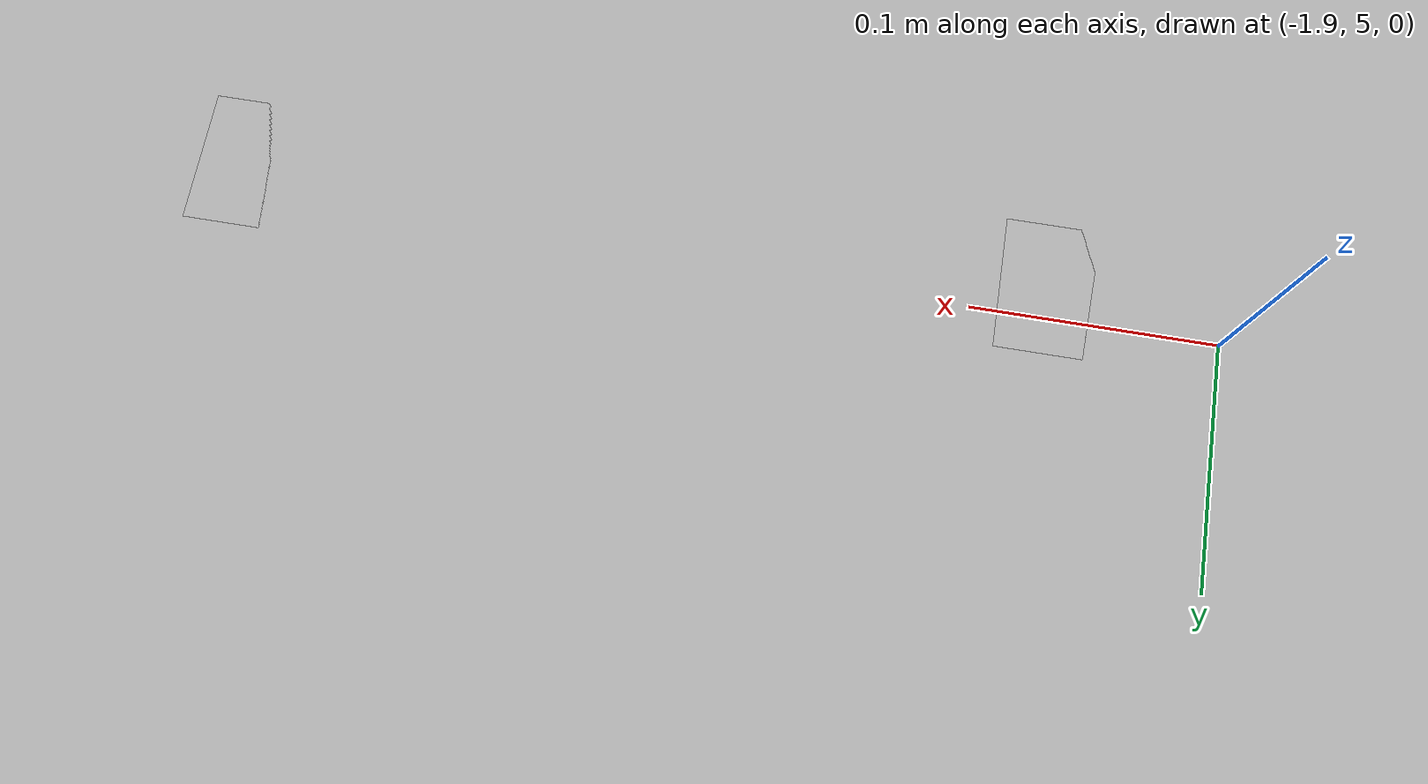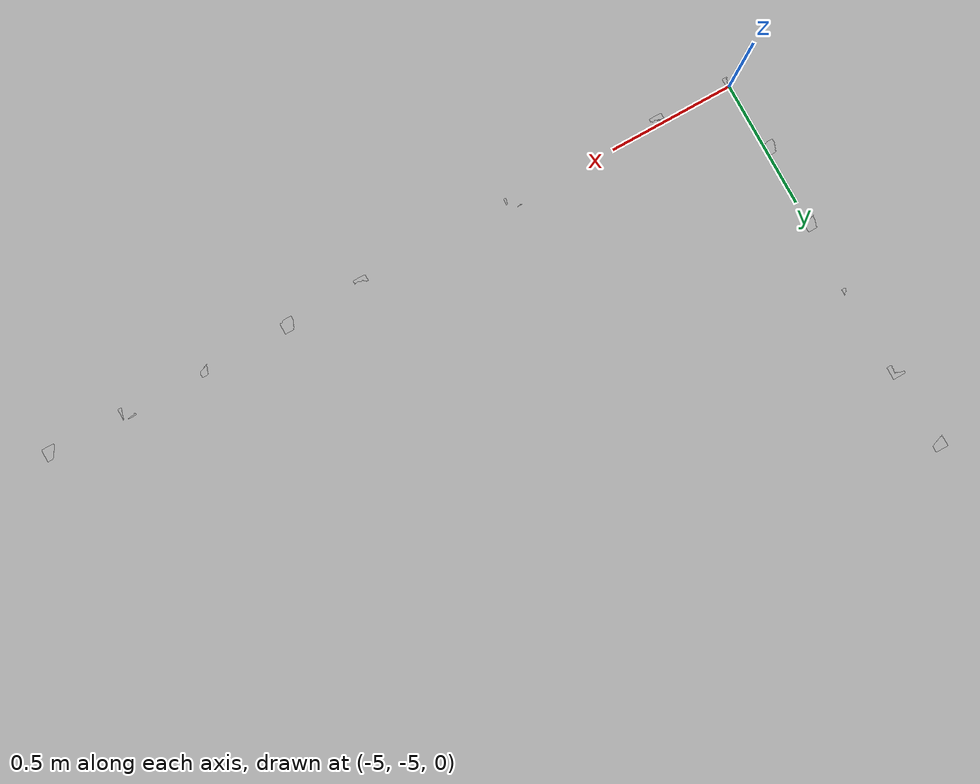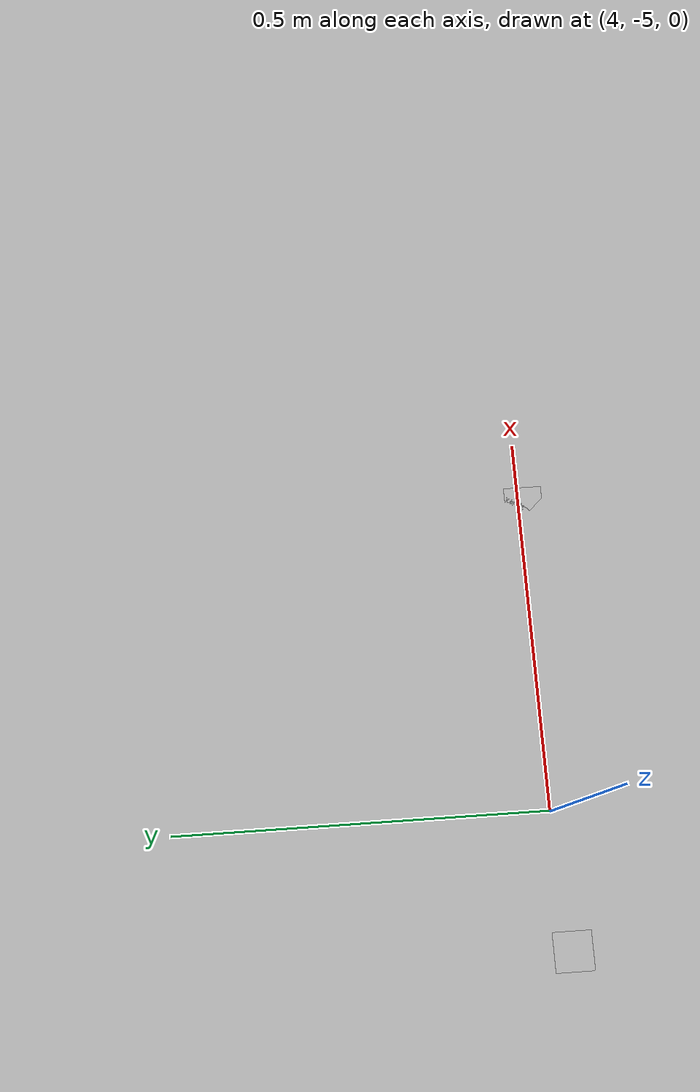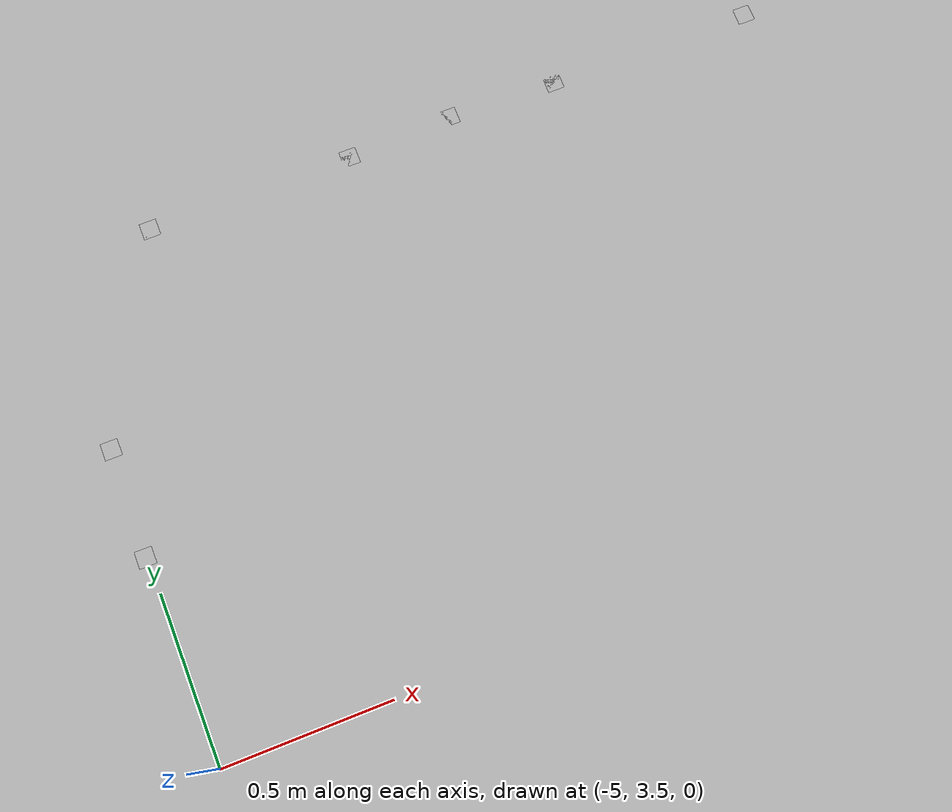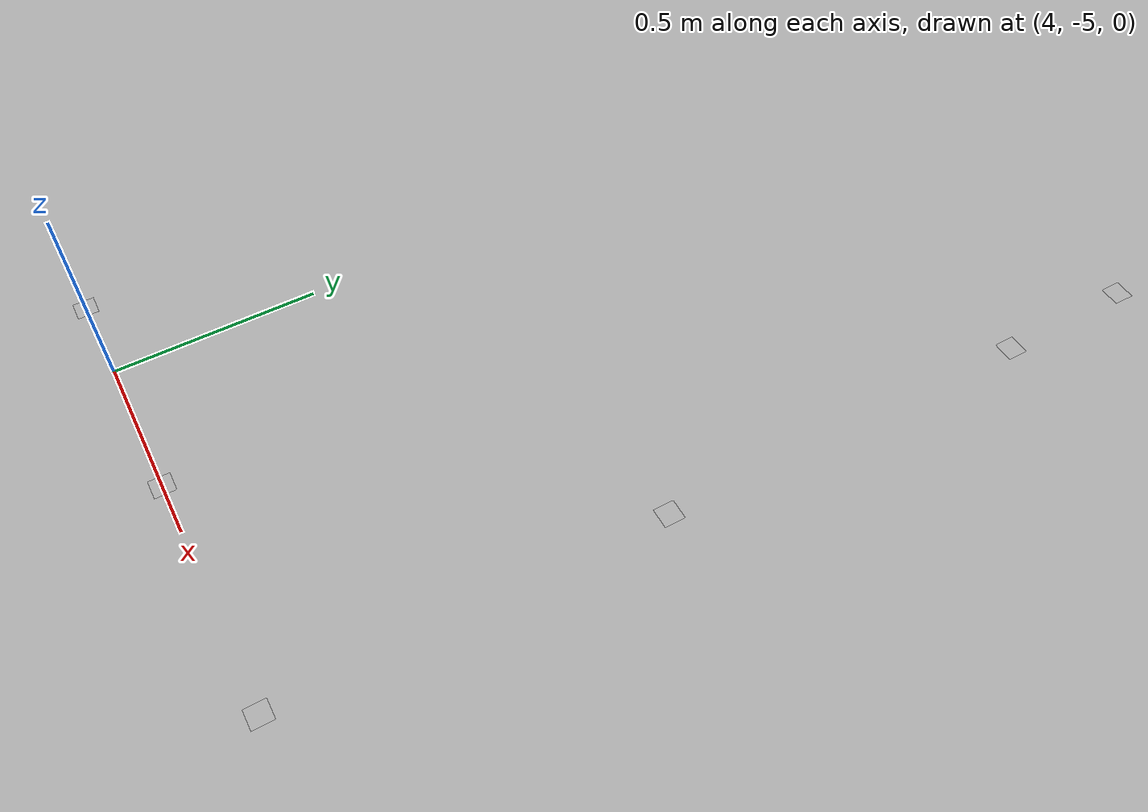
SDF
<sdf version="1.6">
 <world name="default">
  <model name="ground_plane">
   <static>1</static>
   <link name="link">
    <collision name="collision">
     <geometry><plane><normal>0 0 1</normal><size>100 100</size></plane></geometry>
     <surface><friction><ode><mu>100</mu><mu2>50</mu2></ode></friction></surface>
    </collision>
    <visual name="visual">
     <cast_shadows>0</cast_shadows>
     <geometry><plane><normal>0 0 1</normal><size>100 100</size></plane></geometry>
     <material>
      <script><uri>file://media/materials/scripts/gazebo.material</uri><name>Gazebo/Grey</name></script>
     </material>
    </visual>
   </link>
  </model>
  <light name="sun" type="directional">
   <pose>0 0 10 0 -0 0</pose>
   <diffuse>0.8 0.8 0.8 1</diffuse>
   <specular>0.1 0.1 0.1 1</specular>
   <attenuation>
    <range>1000</range>
    <constant>0.9</constant>
    <linear>0.01</linear>
    <quadratic>0.001</quadratic>
   </attenuation>
   <direction>-0.5 0.5 -1</direction>
  </light>
  <plugin name="SetupWorld" filename="libgazebo_plugins.so"/>
  <gravity>0 0 -9.8</gravity>
  <magnetic_field>6e-06 2.3e-05 -4.2e-05</magnetic_field>
  <atmosphere type="adiabatic"/>
  <physics name="default_physics" default="0" type="ode">
   <max_step_size>0.001</max_step_size>
   <real_time_factor>1</real_time_factor>
   <real_time_update_rate>1000</real_time_update_rate>
  </physics>
  <scene><ambient>0.4 0.4 0.4 1</ambient><background>0.7 0.7 0.7 1</background><shadows>1</shadows></scene>
  <spherical_coordinates>
   <surface_model>EARTH_WGS84</surface_model>
   <latitude_deg>0</latitude_deg>
   <longitude_deg>0</longitude_deg>
   <elevation>0</elevation>
   <heading_deg>0</heading_deg>
  </spherical_coordinates>
  <model name="concrete_ground_plane">
   <static>1</static>
   <link name="link">
    <collision name="collision">
     <geometry><plane><normal>0 0 1</normal><size>100 100</size></plane></geometry>
     <surface><friction><ode><mu>100</mu><mu2>50</mu2></ode></friction></surface>
    </collision>
    <visual name="visual">
     <cast_shadows>0</cast_shadows>
     <geometry><plane><normal>0 0 1</normal><size>100 100</size></plane></geometry>
     <material>
      <script>
       <uri>model://media/materials/scripts</uri>
       <uri>model://media/materials/textures</uri>
       <name>ConcreteGroundPlane/Image</name>
      </script>
     </material>
    </visual>
   </link>
  </model>
  <model name="collection_disk">
   <static>1</static>
   <link name="link">
    <visual name="visual">
     <geometry><box><size>1.016 1.016 0.001</size></box></geometry>
     <material>
      <script>
       <uri>model://collection_disk/materials/scripts</uri>
       <uri>model://collection_disk/materials/textures</uri>
       <name>collection_disk/Diffuse</name>
      </script>
     </material>
    </visual>
   </link>
   <plugin name="score_sim" filename="libgazebo_plugins_score.so">
    <scoreTopic>/collectionZone/score</scoreTopic>
    <collectionZoneSquareSize>1.016</collectionZoneSquareSize>
    <updateRate>0.2</updateRate>
    <robotNamespace>/</robotNamespace>
   </plugin>
  </model>
  <model name="at0">
   <static>0</static>
   <link name="link">
    <inertial>
     <mass>0.01</mass>
     <inertia><ixx>4e-05</ixx><ixy>0</ixy><ixz>0</ixz><iyy>4e-05</iyy><iyz>0</iyz><izz>4e-05</izz></inertia>
    </inertial>
    <visual name="visual">
     <geometry><box><size>0.05 0.05 0.05</size></box></geometry>
     <material>
      <script>
       <uri>model://at0/materials/scripts</uri>
       <uri>model://at0/materials/textures</uri>
       <name>at0/Diffuse</name>
      </script>
     </material>
    </visual>
    <collision name="collision">
     <geometry><box><size>0.05 0.05 0.05</size></box></geometry>
     <surface><friction><ode><mu>0.8</mu><mu2>0.7</mu2></ode></friction></surface>
    </collision>
   </link>
   <pose>-4.9988 0.063371 0.02499 0 2e-06 0</pose>
  </model>
  <model name="at0_0">
   <static>0</static>
   <link name="link">
    <inertial>
     <mass>0.01</mass>
     <inertia><ixx>4e-05</ixx><ixy>0</ixy><ixz>0</ixz><iyy>4e-05</iyy><iyz>0</iyz><izz>4e-05</izz></inertia>
    </inertial>
    <visual name="visual">
     <geometry><box><size>0.05 0.05 0.05</size></box></geometry>
     <material>
      <script>
       <uri>model://at0/materials/scripts</uri>
       <uri>model://at0/materials/textures</uri>
       <name>at0/Diffuse</name>
      </script>
     </material>
    </visual>
    <collision name="collision">
     <geometry><box><size>0.05 0.05 0.05</size></box></geometry>
     <surface><friction><ode><mu>0.8</mu><mu2>0.7</mu2></ode></friction></surface>
    </collision>
   </link>
   <pose>-4.99951 -5.0028 0.025 0 -2e-06 0</pose>
  </model>
  <model name="at0_1">
   <static>0</static>
   <link name="link">
    <inertial>
     <mass>0.01</mass>
     <inertia><ixx>4e-05</ixx><ixy>0</ixy><ixz>0</ixz><iyy>4e-05</iyy><iyz>0</iyz><izz>4e-05</izz></inertia>
    </inertial>
    <visual name="visual">
     <geometry><box><size>0.05 0.05 0.05</size></box></geometry>
     <material>
      <script>
       <uri>model://at0/materials/scripts</uri>
       <uri>model://at0/materials/textures</uri>
       <name>at0/Diffuse</name>
      </script>
     </material>
    </visual>
    <collision name="collision">
     <geometry><box><size>0.05 0.05 0.05</size></box></geometry>
     <surface><friction><ode><mu>0.8</mu><mu2>0.7</mu2></ode></friction></surface>
    </collision>
   </link>
   <pose>-5.00374 5.00624 0.02499 0 2e-06 0</pose>
  </model>
  <model name="at0_2">
   <static>0</static>
   <link name="link">
    <inertial>
     <mass>0.01</mass>
     <inertia><ixx>4e-05</ixx><ixy>0</ixy><ixz>0</ixz><iyy>4e-05</iyy><iyz>0</iyz><izz>4e-05</izz></inertia>
    </inertial>
    <visual name="visual">
     <geometry><box><size>0.05 0.05 0.05</size></box></geometry>
     <material>
      <script>
       <uri>model://at0/materials/scripts</uri>
       <uri>model://at0/materials/textures</uri>
       <name>at0/Diffuse</name>
      </script>
     </material>
    </visual>
    <collision name="collision">
     <geometry><box><size>0.05 0.05 0.05</size></box></geometry>
     <surface><friction><ode><mu>0.8</mu><mu2>0.7</mu2></ode></friction></surface>
    </collision>
   </link>
   <pose>5.0006 0.00199 0.025 0 -2e-06 0</pose>
  </model>
  <model name="at0_3">
   <static>0</static>
   <link name="link">
    <inertial>
     <mass>0.01</mass>
     <inertia><ixx>4e-05</ixx><ixy>0</ixy><ixz>0</ixz><iyy>4e-05</iyy><iyz>0</iyz><izz>4e-05</izz></inertia>
    </inertial>
    <visual name="visual">
     <geometry><box><size>0.05 0.05 0.05</size></box></geometry>
     <material>
      <script>
       <uri>model://at0/materials/scripts</uri>
       <uri>model://at0/materials/textures</uri>
       <name>at0/Diffuse</name>
      </script>
     </material>
    </visual>
    <collision name="collision">
     <geometry><box><size>0.05 0.05 0.05</size></box></geometry>
     <surface><friction><ode><mu>0.8</mu><mu2>0.7</mu2></ode></friction></surface>
    </collision>
   </link>
   <pose>4.99634 5.00528 0.02499 0 2e-06 0</pose>
  </model>
  <model name="at0_4">
   <static>0</static>
   <link name="link">
    <inertial>
     <mass>0.01</mass>
     <inertia><ixx>4e-05</ixx><ixy>0</ixy><ixz>0</ixz><iyy>4e-05</iyy><iyz>0</iyz><izz>4e-05</izz></inertia>
    </inertial>
    <visual name="visual">
     <geometry><box><size>0.05 0.05 0.05</size></box></geometry>
     <material>
      <script>
       <uri>model://at0/materials/scripts</uri>
       <uri>model://at0/materials/textures</uri>
       <name>at0/Diffuse</name>
      </script>
     </material>
    </visual>
    <collision name="collision">
     <geometry><box><size>0.05 0.05 0.05</size></box></geometry>
     <surface><friction><ode><mu>0.8</mu><mu2>0.7</mu2></ode></friction></surface>
    </collision>
   </link>
   <pose>4.99975 -4.99656 0.025 0 -2e-06 0</pose>
  </model>
  <model name="at0_5">
   <static>0</static>
   <link name="link">
    <inertial>
     <mass>0.01</mass>
     <inertia><ixx>4e-05</ixx><ixy>0</ixy><ixz>0</ixz><iyy>4e-05</iyy><iyz>0</iyz><izz>4e-05</izz></inertia>
    </inertial>
    <visual name="visual">
     <geometry><box><size>0.05 0.05 0.05</size></box></geometry>
     <material>
      <script>
       <uri>model://at0/materials/scripts</uri>
       <uri>model://at0/materials/textures</uri>
       <name>at0/Diffuse</name>
      </script>
     </material>
    </visual>
    <collision name="collision">
     <geometry><box><size>0.05 0.05 0.05</size></box></geometry>
     <surface><friction><ode><mu>0.8</mu><mu2>0.7</mu2></ode></friction></surface>
    </collision>
   </link>
   <pose>0.00289 -4.99668 0.02499 0 2e-06 0</pose>
  </model>
  <model name="at0_6">
   <static>0</static>
   <link name="link">
    <inertial>
     <mass>0.01</mass>
     <inertia><ixx>4e-05</ixx><ixy>0</ixy><ixz>0</ixz><iyy>4e-05</iyy><iyz>0</iyz><izz>4e-05</izz></inertia>
    </inertial>
    <visual name="visual">
     <geometry><box><size>0.05 0.05 0.05</size></box></geometry>
     <material>
      <script>
       <uri>model://at0/materials/scripts</uri>
       <uri>model://at0/materials/textures</uri>
       <name>at0/Diffuse</name>
      </script>
     </material>
    </visual>
    <collision name="collision">
     <geometry><box><size>0.05 0.05 0.05</size></box></geometry>
     <surface><friction><ode><mu>0.8</mu><mu2>0.7</mu2></ode></friction></surface>
    </collision>
   </link>
   <pose>0.004995 5.0075 0.025 0 -2e-06 0</pose>
  </model>
  <model name="at0_7">
   <static>0</static>
   <link name="link">
    <inertial>
     <mass>0.01</mass>
     <inertia><ixx>4e-05</ixx><ixy>0</ixy><ixz>0</ixz><iyy>4e-05</iyy><iyz>0</iyz><izz>4e-05</izz></inertia>
    </inertial>
    <visual name="visual">
     <geometry><box><size>0.05 0.05 0.05</size></box></geometry>
     <material>
      <script>
       <uri>model://at0/materials/scripts</uri>
       <uri>model://at0/materials/textures</uri>
       <name>at0/Diffuse</name>
      </script>
     </material>
    </visual>
    <collision name="collision">
     <geometry><box><size>0.05 0.05 0.05</size></box></geometry>
     <surface><friction><ode><mu>0.8</mu><mu2>0.7</mu2></ode></friction></surface>
    </collision>
   </link>
   <pose>-2.47271 5.00301 0.02499 0 2e-06 0</pose>
  </model>
  <model name="at0_8">
   <static>0</static>
   <link name="link">
    <inertial>
     <mass>0.01</mass>
     <inertia><ixx>4e-05</ixx><ixy>0</ixy><ixz>0</ixz><iyy>4e-05</iyy><iyz>0</iyz><izz>4e-05</izz></inertia>
    </inertial>
    <visual name="visual">
     <geometry><box><size>0.05 0.05 0.05</size></box></geometry>
     <material>
      <script>
       <uri>model://at0/materials/scripts</uri>
       <uri>model://at0/materials/textures</uri>
       <name>at0/Diffuse</name>
      </script>
     </material>
    </visual>
    <collision name="collision">
     <geometry><box><size>0.05 0.05 0.05</size></box></geometry>
     <surface><friction><ode><mu>0.8</mu><mu2>0.7</mu2></ode></friction></surface>
    </collision>
   </link>
   <pose>2.52217 5.00215 0.025 0 -2e-06 0</pose>
  </model>
  <model name="at0_9">
   <static>0</static>
   <link name="link">
    <inertial>
     <mass>0.01</mass>
     <inertia><ixx>4e-05</ixx><ixy>0</ixy><ixz>0</ixz><iyy>4e-05</iyy><iyz>0</iyz><izz>4e-05</izz></inertia>
    </inertial>
    <visual name="visual">
     <geometry><box><size>0.05 0.05 0.05</size></box></geometry>
     <material>
      <script>
       <uri>model://at0/materials/scripts</uri>
       <uri>model://at0/materials/textures</uri>
       <name>at0/Diffuse</name>
      </script>
     </material>
    </visual>
    <collision name="collision">
     <geometry><box><size>0.05 0.05 0.05</size></box></geometry>
     <surface><friction><ode><mu>0.8</mu><mu2>0.7</mu2></ode></friction></surface>
    </collision>
   </link>
   <pose>5.0017 2.49657 0.02499 0 2e-06 0</pose>
  </model>
  <model name="at0_10">
   <static>0</static>
   <link name="link">
    <inertial>
     <mass>0.01</mass>
     <inertia><ixx>4e-05</ixx><ixy>0</ixy><ixz>0</ixz><iyy>4e-05</iyy><iyz>0</iyz><izz>4e-05</izz></inertia>
    </inertial>
    <visual name="visual">
     <geometry><box><size>0.05 0.05 0.05</size></box></geometry>
     <material>
      <script>
       <uri>model://at0/materials/scripts</uri>
       <uri>model://at0/materials/textures</uri>
       <name>at0/Diffuse</name>
      </script>
     </material>
    </visual>
    <collision name="collision">
     <geometry><box><size>0.05 0.05 0.05</size></box></geometry>
     <surface><friction><ode><mu>0.8</mu><mu2>0.7</mu2></ode></friction></surface>
    </collision>
   </link>
   <pose>5.00642 -2.48809 0.025 0 -2e-06 0</pose>
  </model>
  <model name="at0_11">
   <static>0</static>
   <link name="link">
    <inertial>
     <mass>0.01</mass>
     <inertia><ixx>4e-05</ixx><ixy>0</ixy><ixz>0</ixz><iyy>4e-05</iyy><iyz>0</iyz><izz>4e-05</izz></inertia>
    </inertial>
    <visual name="visual">
     <geometry><box><size>0.05 0.05 0.05</size></box></geometry>
     <material>
      <script>
       <uri>model://at0/materials/scripts</uri>
       <uri>model://at0/materials/textures</uri>
       <name>at0/Diffuse</name>
      </script>
     </material>
    </visual>
    <collision name="collision">
     <geometry><box><size>0.05 0.05 0.05</size></box></geometry>
     <surface><friction><ode><mu>0.8</mu><mu2>0.7</mu2></ode></friction></surface>
    </collision>
   </link>
   <pose>2.54606 -4.99664 0.02499 0 2e-06 0</pose>
  </model>
  <model name="at0_12">
   <static>0</static>
   <link name="link">
    <inertial>
     <mass>0.01</mass>
     <inertia><ixx>4e-05</ixx><ixy>0</ixy><ixz>0</ixz><iyy>4e-05</iyy><iyz>0</iyz><izz>4e-05</izz></inertia>
    </inertial>
    <visual name="visual">
     <geometry><box><size>0.05 0.05 0.05</size></box></geometry>
     <material>
      <script>
       <uri>model://at0/materials/scripts</uri>
       <uri>model://at0/materials/textures</uri>
       <name>at0/Diffuse</name>
      </script>
     </material>
    </visual>
    <collision name="collision">
     <geometry><box><size>0.05 0.05 0.05</size></box></geometry>
     <surface><friction><ode><mu>0.8</mu><mu2>0.7</mu2></ode></friction></surface>
    </collision>
   </link>
   <pose>-2.46375 -5.00363 0.025 0 -2e-06 0</pose>
  </model>
  <model name="at0_13">
   <static>0</static>
   <link name="link">
    <inertial>
     <mass>0.01</mass>
     <inertia><ixx>4e-05</ixx><ixy>0</ixy><ixz>0</ixz><iyy>4e-05</iyy><iyz>0</iyz><izz>4e-05</izz></inertia>
    </inertial>
    <visual name="visual">
     <geometry><box><size>0.05 0.05 0.05</size></box></geometry>
     <material>
      <script>
       <uri>model://at0/materials/scripts</uri>
       <uri>model://at0/materials/textures</uri>
       <name>at0/Diffuse</name>
      </script>
     </material>
    </visual>
    <collision name="collision">
     <geometry><box><size>0.05 0.05 0.05</size></box></geometry>
     <surface><friction><ode><mu>0.8</mu><mu2>0.7</mu2></ode></friction></surface>
    </collision>
   </link>
   <pose>-4.99918 -2.50188 0.02499 0 2e-06 0</pose>
  </model>
  <model name="at0_14">
   <static>0</static>
   <link name="link">
    <inertial>
     <mass>0.01</mass>
     <inertia><ixx>4e-05</ixx><ixy>0</ixy><ixz>0</ixz><iyy>4e-05</iyy><iyz>0</iyz><izz>4e-05</izz></inertia>
    </inertial>
    <visual name="visual">
     <geometry><box><size>0.05 0.05 0.05</size></box></geometry>
     <material>
      <script>
       <uri>model://at0/materials/scripts</uri>
       <uri>model://at0/materials/textures</uri>
       <name>at0/Diffuse</name>
      </script>
     </material>
    </visual>
    <collision name="collision">
     <geometry><box><size>0.05 0.05 0.05</size></box></geometry>
     <surface><friction><ode><mu>0.8</mu><mu2>0.7</mu2></ode></friction></surface>
    </collision>
   </link>
   <pose>-4.99864 2.55671 0.025 0 -2e-06 0</pose>
  </model>
  <model name="at0_15">
   <static>0</static>
   <link name="link">
    <inertial>
     <mass>0.01</mass>
     <inertia><ixx>4e-05</ixx><ixy>0</ixy><ixz>0</ixz><iyy>4e-05</iyy><iyz>0</iyz><izz>4e-05</izz></inertia>
    </inertial>
    <visual name="visual">
     <geometry><box><size>0.05 0.05 0.05</size></box></geometry>
     <material>
      <script>
       <uri>model://at0/materials/scripts</uri>
       <uri>model://at0/materials/textures</uri>
       <name>at0/Diffuse</name>
      </script>
     </material>
    </visual>
    <collision name="collision">
     <geometry><box><size>0.05 0.05 0.05</size></box></geometry>
     <surface><friction><ode><mu>0.8</mu><mu2>0.7</mu2></ode></friction></surface>
    </collision>
   </link>
   <pose>-4.99883 3.76425 0.02499 0 2e-06 0</pose>
  </model>
  <model name="at0_16">
   <static>0</static>
   <link name="link">
    <inertial>
     <mass>0.01</mass>
     <inertia><ixx>4e-05</ixx><ixy>0</ixy><ixz>0</ixz><iyy>4e-05</iyy><iyz>0</iyz><izz>4e-05</izz></inertia>
    </inertial>
    <visual name="visual">
     <geometry><box><size>0.05 0.05 0.05</size></box></geometry>
     <material>
      <script>
       <uri>model://at0/materials/scripts</uri>
       <uri>model://at0/materials/textures</uri>
       <name>at0/Diffuse</name>
      </script>
     </material>
    </visual>
    <collision name="collision">
     <geometry><box><size>0.05 0.05 0.05</size></box></geometry>
     <surface><friction><ode><mu>0.8</mu><mu2>0.7</mu2></ode></friction></surface>
    </collision>
   </link>
   <pose>-3.75267 5.01115 0.025 0 -2e-06 0</pose>
  </model>
  <model name="at0_17">
   <static>0</static>
   <link name="link">
    <inertial>
     <mass>0.01</mass>
     <inertia><ixx>4e-05</ixx><ixy>0</ixy><ixz>0</ixz><iyy>4e-05</iyy><iyz>0</iyz><izz>4e-05</izz></inertia>
    </inertial>
    <visual name="visual">
     <geometry><box><size>0.05 0.05 0.05</size></box></geometry>
     <material>
      <script>
       <uri>model://at0/materials/scripts</uri>
       <uri>model://at0/materials/textures</uri>
       <name>at0/Diffuse</name>
      </script>
     </material>
    </visual>
    <collision name="collision">
     <geometry><box><size>0.05 0.05 0.05</size></box></geometry>
     <surface><friction><ode><mu>0.8</mu><mu2>0.7</mu2></ode></friction></surface>
    </collision>
   </link>
   <pose>-1.19701 4.99631 0.02499 0 2e-06 0</pose>
  </model>
  <model name="at0_18">
   <static>0</static>
   <link name="link">
    <inertial>
     <mass>0.01</mass>
     <inertia><ixx>4e-05</ixx><ixy>0</ixy><ixz>0</ixz><iyy>4e-05</iyy><iyz>0</iyz><izz>4e-05</izz></inertia>
    </inertial>
    <visual name="visual">
     <geometry><box><size>0.05 0.05 0.05</size></box></geometry>
     <material>
      <script>
       <uri>model://at0/materials/scripts</uri>
       <uri>model://at0/materials/textures</uri>
       <name>at0/Diffuse</name>
      </script>
     </material>
    </visual>
    <collision name="collision">
     <geometry><box><size>0.05 0.05 0.05</size></box></geometry>
     <surface><friction><ode><mu>0.8</mu><mu2>0.7</mu2></ode></friction></surface>
    </collision>
   </link>
   <pose>1.21842 5.00774 0.025 0 -2e-06 0</pose>
  </model>
  <model name="at0_19">
   <static>0</static>
   <link name="link">
    <inertial>
     <mass>0.01</mass>
     <inertia><ixx>4e-05</ixx><ixy>0</ixy><ixz>0</ixz><iyy>4e-05</iyy><iyz>0</iyz><izz>4e-05</izz></inertia>
    </inertial>
    <visual name="visual">
     <geometry><box><size>0.05 0.05 0.05</size></box></geometry>
     <material>
      <script>
       <uri>model://at0/materials/scripts</uri>
       <uri>model://at0/materials/textures</uri>
       <name>at0/Diffuse</name>
      </script>
     </material>
    </visual>
    <collision name="collision">
     <geometry><box><size>0.05 0.05 0.05</size></box></geometry>
     <surface><friction><ode><mu>0.8</mu><mu2>0.7</mu2></ode></friction></surface>
    </collision>
   </link>
   <pose>3.75938 5.00038 0.02499 0 2e-06 0</pose>
  </model>
  <model name="at0_20">
   <static>0</static>
   <link name="link">
    <inertial>
     <mass>0.01</mass>
     <inertia><ixx>4e-05</ixx><ixy>0</ixy><ixz>0</ixz><iyy>4e-05</iyy><iyz>0</iyz><izz>4e-05</izz></inertia>
    </inertial>
    <visual name="visual">
     <geometry><box><size>0.05 0.05 0.05</size></box></geometry>
     <material>
      <script>
       <uri>model://at0/materials/scripts</uri>
       <uri>model://at0/materials/textures</uri>
       <name>at0/Diffuse</name>
      </script>
     </material>
    </visual>
    <collision name="collision">
     <geometry><box><size>0.05 0.05 0.05</size></box></geometry>
     <surface><friction><ode><mu>0.8</mu><mu2>0.7</mu2></ode></friction></surface>
    </collision>
   </link>
   <pose>5.00366 3.82723 0.025 0 -2e-06 0</pose>
  </model>
  <model name="at0_21">
   <static>0</static>
   <link name="link">
    <inertial>
     <mass>0.01</mass>
     <inertia><ixx>4e-05</ixx><ixy>0</ixy><ixz>0</ixz><iyy>4e-05</iyy><iyz>0</iyz><izz>4e-05</izz></inertia>
    </inertial>
    <visual name="visual">
     <geometry><box><size>0.05 0.05 0.05</size></box></geometry>
     <material>
      <script>
       <uri>model://at0/materials/scripts</uri>
       <uri>model://at0/materials/textures</uri>
       <name>at0/Diffuse</name>
      </script>
     </material>
    </visual>
    <collision name="collision">
     <geometry><box><size>0.05 0.05 0.05</size></box></geometry>
     <surface><friction><ode><mu>0.8</mu><mu2>0.7</mu2></ode></friction></surface>
    </collision>
   </link>
   <pose>5.00343 1.21104 0.02499 0 2e-06 0</pose>
  </model>
  <model name="at0_22">
   <static>0</static>
   <link name="link">
    <inertial>
     <mass>0.01</mass>
     <inertia><ixx>4e-05</ixx><ixy>0</ixy><ixz>0</ixz><iyy>4e-05</iyy><iyz>0</iyz><izz>4e-05</izz></inertia>
    </inertial>
    <visual name="visual">
     <geometry><box><size>0.05 0.05 0.05</size></box></geometry>
     <material>
      <script>
       <uri>model://at0/materials/scripts</uri>
       <uri>model://at0/materials/textures</uri>
       <name>at0/Diffuse</name>
      </script>
     </material>
    </visual>
    <collision name="collision">
     <geometry><box><size>0.05 0.05 0.05</size></box></geometry>
     <surface><friction><ode><mu>0.8</mu><mu2>0.7</mu2></ode></friction></surface>
    </collision>
   </link>
   <pose>5.00202 -1.15834 0.025 0 -2e-06 0</pose>
  </model>
  <model name="at0_23">
   <static>0</static>
   <link name="link">
    <inertial>
     <mass>0.01</mass>
     <inertia><ixx>4e-05</ixx><ixy>0</ixy><ixz>0</ixz><iyy>4e-05</iyy><iyz>0</iyz><izz>4e-05</izz></inertia>
    </inertial>
    <visual name="visual">
     <geometry><box><size>0.05 0.05 0.05</size></box></geometry>
     <material>
      <script>
       <uri>model://at0/materials/scripts</uri>
       <uri>model://at0/materials/textures</uri>
       <name>at0/Diffuse</name>
      </script>
     </material>
    </visual>
    <collision name="collision">
     <geometry><box><size>0.05 0.05 0.05</size></box></geometry>
     <surface><friction><ode><mu>0.8</mu><mu2>0.7</mu2></ode></friction></surface>
    </collision>
   </link>
   <pose>4.99802 -3.75494 0.02499 0 2e-06 0</pose>
  </model>
  <model name="at0_24">
   <static>0</static>
   <link name="link">
    <inertial>
     <mass>0.01</mass>
     <inertia><ixx>4e-05</ixx><ixy>0</ixy><ixz>0</ixz><iyy>4e-05</iyy><iyz>0</iyz><izz>4e-05</izz></inertia>
    </inertial>
    <visual name="visual">
     <geometry><box><size>0.05 0.05 0.05</size></box></geometry>
     <material>
      <script>
       <uri>model://at0/materials/scripts</uri>
       <uri>model://at0/materials/textures</uri>
       <name>at0/Diffuse</name>
      </script>
     </material>
    </visual>
    <collision name="collision">
     <geometry><box><size>0.05 0.05 0.05</size></box></geometry>
     <surface><friction><ode><mu>0.8</mu><mu2>0.7</mu2></ode></friction></surface>
    </collision>
   </link>
   <pose>3.82257 -5.0027 0.025 0 -2e-06 0</pose>
  </model>
  <model name="at0_25">
   <static>0</static>
   <link name="link">
    <inertial>
     <mass>0.01</mass>
     <inertia><ixx>4e-05</ixx><ixy>0</ixy><ixz>0</ixz><iyy>4e-05</iyy><iyz>0</iyz><izz>4e-05</izz></inertia>
    </inertial>
    <visual name="visual">
     <geometry><box><size>0.05 0.05 0.05</size></box></geometry>
     <material>
      <script>
       <uri>model://at0/materials/scripts</uri>
       <uri>model://at0/materials/textures</uri>
       <name>at0/Diffuse</name>
      </script>
     </material>
    </visual>
    <collision name="collision">
     <geometry><box><size>0.05 0.05 0.05</size></box></geometry>
     <surface><friction><ode><mu>0.8</mu><mu2>0.7</mu2></ode></friction></surface>
    </collision>
   </link>
   <pose>1.2275 -4.99867 0.02499 0 2e-06 0</pose>
  </model>
  <model name="at0_26">
   <static>0</static>
   <link name="link">
    <inertial>
     <mass>0.01</mass>
     <inertia><ixx>4e-05</ixx><ixy>0</ixy><ixz>0</ixz><iyy>4e-05</iyy><iyz>0</iyz><izz>4e-05</izz></inertia>
    </inertial>
    <visual name="visual">
     <geometry><box><size>0.05 0.05 0.05</size></box></geometry>
     <material>
      <script>
       <uri>model://at0/materials/scripts</uri>
       <uri>model://at0/materials/textures</uri>
       <name>at0/Diffuse</name>
      </script>
     </material>
    </visual>
    <collision name="collision">
     <geometry><box><size>0.05 0.05 0.05</size></box></geometry>
     <surface><friction><ode><mu>0.8</mu><mu2>0.7</mu2></ode></friction></surface>
    </collision>
   </link>
   <pose>-1.21994 -5.00214 0.025 0 -2e-06 0</pose>
  </model>
  <model name="at0_27">
   <static>0</static>
   <link name="link">
    <inertial>
     <mass>0.01</mass>
     <inertia><ixx>4e-05</ixx><ixy>0</ixy><ixz>0</ixz><iyy>4e-05</iyy><iyz>0</iyz><izz>4e-05</izz></inertia>
    </inertial>
    <visual name="visual">
     <geometry><box><size>0.05 0.05 0.05</size></box></geometry>
     <material>
      <script>
       <uri>model://at0/materials/scripts</uri>
       <uri>model://at0/materials/textures</uri>
       <name>at0/Diffuse</name>
      </script>
     </material>
    </visual>
    <collision name="collision">
     <geometry><box><size>0.05 0.05 0.05</size></box></geometry>
     <surface><friction><ode><mu>0.8</mu><mu2>0.7</mu2></ode></friction></surface>
    </collision>
   </link>
   <pose>-3.76843 -4.99724 0.02499 0 2e-06 0</pose>
  </model>
  <model name="at0_28">
   <static>0</static>
   <link name="link">
    <inertial>
     <mass>0.01</mass>
     <inertia><ixx>4e-05</ixx><ixy>0</ixy><ixz>0</ixz><iyy>4e-05</iyy><iyz>0</iyz><izz>4e-05</izz></inertia>
    </inertial>
    <visual name="visual">
     <geometry><box><size>0.05 0.05 0.05</size></box></geometry>
     <material>
      <script>
       <uri>model://at0/materials/scripts</uri>
       <uri>model://at0/materials/textures</uri>
       <name>at0/Diffuse</name>
      </script>
     </material>
    </visual>
    <collision name="collision">
     <geometry><box><size>0.05 0.05 0.05</size></box></geometry>
     <surface><friction><ode><mu>0.8</mu><mu2>0.7</mu2></ode></friction></surface>
    </collision>
   </link>
   <pose>-4.99956 -3.77749 0.025 0 -2e-06 0</pose>
  </model>
  <model name="at0_29">
   <static>0</static>
   <link name="link">
    <inertial>
     <mass>0.01</mass>
     <inertia><ixx>4e-05</ixx><ixy>0</ixy><ixz>0</ixz><iyy>4e-05</iyy><iyz>0</iyz><izz>4e-05</izz></inertia>
    </inertial>
    <visual name="visual">
     <geometry><box><size>0.05 0.05 0.05</size></box></geometry>
     <material>
      <script>
       <uri>model://at0/materials/scripts</uri>
       <uri>model://at0/materials/textures</uri>
       <name>at0/Diffuse</name>
      </script>
     </material>
    </visual>
    <collision name="collision">
     <geometry><box><size>0.05 0.05 0.05</size></box></geometry>
     <surface><friction><ode><mu>0.8</mu><mu2>0.7</mu2></ode></friction></surface>
    </collision>
   </link>
   <pose>-4.99031 -1.18645 0.02499 0 2e-06 0</pose>
  </model>
  <model name="at0_45">
   <static>0</static>
   <link name="link">
    <inertial>
     <mass>0.01</mass>
     <inertia><ixx>4e-05</ixx><ixy>0</ixy><ixz>0</ixz><iyy>4e-05</iyy><iyz>0</iyz><izz>4e-05</izz></inertia>
    </inertial>
    <visual name="visual">
     <geometry><box><size>0.05 0.05 0.05</size></box></geometry>
     <material>
      <script>
       <uri>model://at0/materials/scripts</uri>
       <uri>model://at0/materials/textures</uri>
       <name>at0/Diffuse</name>
      </script>
     </material>
    </visual>
    <collision name="collision">
     <geometry><box><size>0.05 0.05 0.05</size></box></geometry>
     <surface><friction><ode><mu>0.8</mu><mu2>0.7</mu2></ode></friction></surface>
    </collision>
   </link>
   <pose>-4.68757 4.99952 0.025 0 -2e-06 0</pose>
  </model>
  <model name="at0_46">
   <static>0</static>
   <link name="link">
    <inertial>
     <mass>0.01</mass>
     <inertia><ixx>4e-05</ixx><ixy>0</ixy><ixz>0</ixz><iyy>4e-05</iyy><iyz>0</iyz><izz>4e-05</izz></inertia>
    </inertial>
    <visual name="visual">
     <geometry><box><size>0.05 0.05 0.05</size></box></geometry>
     <material>
      <script>
       <uri>model://at0/materials/scripts</uri>
       <uri>model://at0/materials/textures</uri>
       <name>at0/Diffuse</name>
      </script>
     </material>
    </visual>
    <collision name="collision">
     <geometry><box><size>0.05 0.05 0.05</size></box></geometry>
     <surface><friction><ode><mu>0.8</mu><mu2>0.7</mu2></ode></friction></surface>
    </collision>
   </link>
   <pose>-4.39568 4.9977 0.02499 0 2e-06 0</pose>
  </model>
  <model name="at0_47">
   <static>0</static>
   <link name="link">
    <inertial>
     <mass>0.01</mass>
     <inertia><ixx>4e-05</ixx><ixy>0</ixy><ixz>0</ixz><iyy>4e-05</iyy><iyz>0</iyz><izz>4e-05</izz></inertia>
    </inertial>
    <visual name="visual">
     <geometry><box><size>0.05 0.05 0.05</size></box></geometry>
     <material>
      <script>
       <uri>model://at0/materials/scripts</uri>
       <uri>model://at0/materials/textures</uri>
       <name>at0/Diffuse</name>
      </script>
     </material>
    </visual>
    <collision name="collision">
     <geometry><box><size>0.05 0.05 0.05</size></box></geometry>
     <surface><friction><ode><mu>0.8</mu><mu2>0.7</mu2></ode></friction></surface>
    </collision>
   </link>
   <pose>-4.0713 4.99887 0.025 0 -2e-06 0</pose>
  </model>
  <model name="at0_48">
   <static>0</static>
   <link name="link">
    <inertial>
     <mass>0.01</mass>
     <inertia><ixx>4e-05</ixx><ixy>0</ixy><ixz>0</ixz><iyy>4e-05</iyy><iyz>0</iyz><izz>4e-05</izz></inertia>
    </inertial>
    <visual name="visual">
     <geometry><box><size>0.05 0.05 0.05</size></box></geometry>
     <material>
      <script>
       <uri>model://at0/materials/scripts</uri>
       <uri>model://at0/materials/textures</uri>
       <name>at0/Diffuse</name>
      </script>
     </material>
    </visual>
    <collision name="collision">
     <geometry><box><size>0.05 0.05 0.05</size></box></geometry>
     <surface><friction><ode><mu>0.8</mu><mu2>0.7</mu2></ode></friction></surface>
    </collision>
   </link>
   <pose>-3.10237 5.00209 0.02499 0 2e-06 0</pose>
  </model>
  <model name="at0_49">
   <static>0</static>
   <link name="link">
    <inertial>
     <mass>0.01</mass>
     <inertia><ixx>4e-05</ixx><ixy>0</ixy><ixz>0</ixz><iyy>4e-05</iyy><iyz>0</iyz><izz>4e-05</izz></inertia>
    </inertial>
    <visual name="visual">
     <geometry><box><size>0.05 0.05 0.05</size></box></geometry>
     <material>
      <script>
       <uri>model://at0/materials/scripts</uri>
       <uri>model://at0/materials/textures</uri>
       <name>at0/Diffuse</name>
      </script>
     </material>
    </visual>
    <collision name="collision">
     <geometry><box><size>0.05 0.05 0.05</size></box></geometry>
     <surface><friction><ode><mu>0.8</mu><mu2>0.7</mu2></ode></friction></surface>
    </collision>
   </link>
   <pose>-1.82811 5.00616 0.025 0 -2e-06 0</pose>
  </model>
  <model name="at0_50">
   <static>0</static>
   <link name="link">
    <inertial>
     <mass>0.01</mass>
     <inertia><ixx>4e-05</ixx><ixy>0</ixy><ixz>0</ixz><iyy>4e-05</iyy><iyz>0</iyz><izz>4e-05</izz></inertia>
    </inertial>
    <visual name="visual">
     <geometry><box><size>0.05 0.05 0.05</size></box></geometry>
     <material>
      <script>
       <uri>model://at0/materials/scripts</uri>
       <uri>model://at0/materials/textures</uri>
       <name>at0/Diffuse</name>
      </script>
     </material>
    </visual>
    <collision name="collision">
     <geometry><box><size>0.05 0.05 0.05</size></box></geometry>
     <surface><friction><ode><mu>0.8</mu><mu2>0.7</mu2></ode></friction></surface>
    </collision>
   </link>
   <pose>-0.600903 5.00427 0.02499 0 2e-06 0</pose>
  </model>
  <model name="at0_51">
   <static>0</static>
   <link name="link">
    <inertial>
     <mass>0.01</mass>
     <inertia><ixx>4e-05</ixx><ixy>0</ixy><ixz>0</ixz><iyy>4e-05</iyy><iyz>0</iyz><izz>4e-05</izz></inertia>
    </inertial>
    <visual name="visual">
     <geometry><box><size>0.05 0.05 0.05</size></box></geometry>
     <material>
      <script>
       <uri>model://at0/materials/scripts</uri>
       <uri>model://at0/materials/textures</uri>
       <name>at0/Diffuse</name>
      </script>
     </material>
    </visual>
    <collision name="collision">
     <geometry><box><size>0.05 0.05 0.05</size></box></geometry>
     <surface><friction><ode><mu>0.8</mu><mu2>0.7</mu2></ode></friction></surface>
    </collision>
   </link>
   <pose>0.62989 4.99779 0.025 0 -2e-06 0</pose>
  </model>
  <model name="at0_52">
   <static>0</static>
   <link name="link">
    <inertial>
     <mass>0.01</mass>
     <inertia><ixx>4e-05</ixx><ixy>0</ixy><ixz>0</ixz><iyy>4e-05</iyy><iyz>0</iyz><izz>4e-05</izz></inertia>
    </inertial>
    <visual name="visual">
     <geometry><box><size>0.05 0.05 0.05</size></box></geometry>
     <material>
      <script>
       <uri>model://at0/materials/scripts</uri>
       <uri>model://at0/materials/textures</uri>
       <name>at0/Diffuse</name>
      </script>
     </material>
    </visual>
    <collision name="collision">
     <geometry><box><size>0.05 0.05 0.05</size></box></geometry>
     <surface><friction><ode><mu>0.8</mu><mu2>0.7</mu2></ode></friction></surface>
    </collision>
   </link>
   <pose>1.87434 5.00476 0.02499 0 2e-06 0</pose>
  </model>
  <model name="at0_53">
   <static>0</static>
   <link name="link">
    <inertial>
     <mass>0.01</mass>
     <inertia><ixx>4e-05</ixx><ixy>0</ixy><ixz>0</ixz><iyy>4e-05</iyy><iyz>0</iyz><izz>4e-05</izz></inertia>
    </inertial>
    <visual name="visual">
     <geometry><box><size>0.05 0.05 0.05</size></box></geometry>
     <material>
      <script>
       <uri>model://at0/materials/scripts</uri>
       <uri>model://at0/materials/textures</uri>
       <name>at0/Diffuse</name>
      </script>
     </material>
    </visual>
    <collision name="collision">
     <geometry><box><size>0.05 0.05 0.05</size></box></geometry>
     <surface><friction><ode><mu>0.8</mu><mu2>0.7</mu2></ode></friction></surface>
    </collision>
   </link>
   <pose>3.19811 4.99767 0.025 0 -2e-06 0</pose>
  </model>
  <model name="at0_54">
   <static>0</static>
   <link name="link">
    <inertial>
     <mass>0.01</mass>
     <inertia><ixx>4e-05</ixx><ixy>0</ixy><ixz>0</ixz><iyy>4e-05</iyy><iyz>0</iyz><izz>4e-05</izz></inertia>
    </inertial>
    <visual name="visual">
     <geometry><box><size>0.05 0.05 0.05</size></box></geometry>
     <material>
      <script>
       <uri>model://at0/materials/scripts</uri>
       <uri>model://at0/materials/textures</uri>
       <name>at0/Diffuse</name>
      </script>
     </material>
    </visual>
    <collision name="collision">
     <geometry><box><size>0.05 0.05 0.05</size></box></geometry>
     <surface><friction><ode><mu>0.8</mu><mu2>0.7</mu2></ode></friction></surface>
    </collision>
   </link>
   <pose>4.36056 5.00217 0.02499 0 2e-06 0</pose>
  </model>
  <model name="at0_55">
   <static>0</static>
   <link name="link">
    <inertial>
     <mass>0.01</mass>
     <inertia><ixx>4e-05</ixx><ixy>0</ixy><ixz>0</ixz><iyy>4e-05</iyy><iyz>0</iyz><izz>4e-05</izz></inertia>
    </inertial>
    <visual name="visual">
     <geometry><box><size>0.05 0.05 0.05</size></box></geometry>
     <material>
      <script>
       <uri>model://at0/materials/scripts</uri>
       <uri>model://at0/materials/textures</uri>
       <name>at0/Diffuse</name>
      </script>
     </material>
    </visual>
    <collision name="collision">
     <geometry><box><size>0.05 0.05 0.05</size></box></geometry>
     <surface><friction><ode><mu>0.8</mu><mu2>0.7</mu2></ode></friction></surface>
    </collision>
   </link>
   <pose>5.00389 4.43577 0.025 0 -2e-06 0</pose>
  </model>
  <model name="at0_56">
   <static>0</static>
   <link name="link">
    <inertial>
     <mass>0.01</mass>
     <inertia><ixx>4e-05</ixx><ixy>0</ixy><ixz>0</ixz><iyy>4e-05</iyy><iyz>0</iyz><izz>4e-05</izz></inertia>
    </inertial>
    <visual name="visual">
     <geometry><box><size>0.05 0.05 0.05</size></box></geometry>
     <material>
      <script>
       <uri>model://at0/materials/scripts</uri>
       <uri>model://at0/materials/textures</uri>
       <name>at0/Diffuse</name>
      </script>
     </material>
    </visual>
    <collision name="collision">
     <geometry><box><size>0.05 0.05 0.05</size></box></geometry>
     <surface><friction><ode><mu>0.8</mu><mu2>0.7</mu2></ode></friction></surface>
    </collision>
   </link>
   <pose>5.00639 3.17375 0.02499 0 2e-06 0</pose>
  </model>
  <model name="at0_57">
   <static>0</static>
   <link name="link">
    <inertial>
     <mass>0.01</mass>
     <inertia><ixx>4e-05</ixx><ixy>0</ixy><ixz>0</ixz><iyy>4e-05</iyy><iyz>0</iyz><izz>4e-05</izz></inertia>
    </inertial>
    <visual name="visual">
     <geometry><box><size>0.05 0.05 0.05</size></box></geometry>
     <material>
      <script>
       <uri>model://at0/materials/scripts</uri>
       <uri>model://at0/materials/textures</uri>
       <name>at0/Diffuse</name>
      </script>
     </material>
    </visual>
    <collision name="collision">
     <geometry><box><size>0.05 0.05 0.05</size></box></geometry>
     <surface><friction><ode><mu>0.8</mu><mu2>0.7</mu2></ode></friction></surface>
    </collision>
   </link>
   <pose>5.00321 1.82304 0.025 0 -2e-06 0</pose>
  </model>
  <model name="at0_58">
   <static>0</static>
   <link name="link">
    <inertial>
     <mass>0.01</mass>
     <inertia><ixx>4e-05</ixx><ixy>0</ixy><ixz>0</ixz><iyy>4e-05</iyy><iyz>0</iyz><izz>4e-05</izz></inertia>
    </inertial>
    <visual name="visual">
     <geometry><box><size>0.05 0.05 0.05</size></box></geometry>
     <material>
      <script>
       <uri>model://at0/materials/scripts</uri>
       <uri>model://at0/materials/textures</uri>
       <name>at0/Diffuse</name>
      </script>
     </material>
    </visual>
    <collision name="collision">
     <geometry><box><size>0.05 0.05 0.05</size></box></geometry>
     <surface><friction><ode><mu>0.8</mu><mu2>0.7</mu2></ode></friction></surface>
    </collision>
   </link>
   <pose>5.00081 0.588268 0.02499 0 2e-06 0</pose>
  </model>
  <model name="at0_59">
   <static>0</static>
   <link name="link">
    <inertial>
     <mass>0.01</mass>
     <inertia><ixx>4e-05</ixx><ixy>0</ixy><ixz>0</ixz><iyy>4e-05</iyy><iyz>0</iyz><izz>4e-05</izz></inertia>
    </inertial>
    <visual name="visual">
     <geometry><box><size>0.05 0.05 0.05</size></box></geometry>
     <material>
      <script>
       <uri>model://at0/materials/scripts</uri>
       <uri>model://at0/materials/textures</uri>
       <name>at0/Diffuse</name>
      </script>
     </material>
    </visual>
    <collision name="collision">
     <geometry><box><size>0.05 0.05 0.05</size></box></geometry>
     <surface><friction><ode><mu>0.8</mu><mu2>0.7</mu2></ode></friction></surface>
    </collision>
   </link>
   <pose>4.99974 -0.558166 0.025 0 -2e-06 0</pose>
  </model>
  <model name="at0_60">
   <static>0</static>
   <link name="link">
    <inertial>
     <mass>0.01</mass>
     <inertia><ixx>4e-05</ixx><ixy>0</ixy><ixz>0</ixz><iyy>4e-05</iyy><iyz>0</iyz><izz>4e-05</izz></inertia>
    </inertial>
    <visual name="visual">
     <geometry><box><size>0.05 0.05 0.05</size></box></geometry>
     <material>
      <script>
       <uri>model://at0/materials/scripts</uri>
       <uri>model://at0/materials/textures</uri>
       <name>at0/Diffuse</name>
      </script>
     </material>
    </visual>
    <collision name="collision">
     <geometry><box><size>0.05 0.05 0.05</size></box></geometry>
     <surface><friction><ode><mu>0.8</mu><mu2>0.7</mu2></ode></friction></surface>
    </collision>
   </link>
   <pose>5.00407 -1.81446 0.02499 0 2e-06 0</pose>
  </model>
  <model name="at0_61">
   <static>0</static>
   <link name="link">
    <inertial>
     <mass>0.01</mass>
     <inertia><ixx>4e-05</ixx><ixy>0</ixy><ixz>0</ixz><iyy>4e-05</iyy><iyz>0</iyz><izz>4e-05</izz></inertia>
    </inertial>
    <visual name="visual">
     <geometry><box><size>0.05 0.05 0.05</size></box></geometry>
     <material>
      <script>
       <uri>model://at0/materials/scripts</uri>
       <uri>model://at0/materials/textures</uri>
       <name>at0/Diffuse</name>
      </script>
     </material>
    </visual>
    <collision name="collision">
     <geometry><box><size>0.05 0.05 0.05</size></box></geometry>
     <surface><friction><ode><mu>0.8</mu><mu2>0.7</mu2></ode></friction></surface>
    </collision>
   </link>
   <pose>5.00447 -3.15023 0.025 0 -2e-06 0</pose>
  </model>
  <model name="at0_62">
   <static>0</static>
   <link name="link">
    <inertial>
     <mass>0.01</mass>
     <inertia><ixx>4e-05</ixx><ixy>0</ixy><ixz>0</ixz><iyy>4e-05</iyy><iyz>0</iyz><izz>4e-05</izz></inertia>
    </inertial>
    <visual name="visual">
     <geometry><box><size>0.05 0.05 0.05</size></box></geometry>
     <material>
      <script>
       <uri>model://at0/materials/scripts</uri>
       <uri>model://at0/materials/textures</uri>
       <name>at0/Diffuse</name>
      </script>
     </material>
    </visual>
    <collision name="collision">
     <geometry><box><size>0.05 0.05 0.05</size></box></geometry>
     <surface><friction><ode><mu>0.8</mu><mu2>0.7</mu2></ode></friction></surface>
    </collision>
   </link>
   <pose>5.0024 -4.36697 0.02499 0 2e-06 0</pose>
  </model>
  <model name="at0_63">
   <static>0</static>
   <link name="link">
    <inertial>
     <mass>0.01</mass>
     <inertia><ixx>4e-05</ixx><ixy>0</ixy><ixz>0</ixz><iyy>4e-05</iyy><iyz>0</iyz><izz>4e-05</izz></inertia>
    </inertial>
    <visual name="visual">
     <geometry><box><size>0.05 0.05 0.05</size></box></geometry>
     <material>
      <script>
       <uri>model://at0/materials/scripts</uri>
       <uri>model://at0/materials/textures</uri>
       <name>at0/Diffuse</name>
      </script>
     </material>
    </visual>
    <collision name="collision">
     <geometry><box><size>0.05 0.05 0.05</size></box></geometry>
     <surface><friction><ode><mu>0.8</mu><mu2>0.7</mu2></ode></friction></surface>
    </collision>
   </link>
   <pose>4.40341 -4.9983 0.025 0 -2e-06 0</pose>
  </model>
  <model name="at0_64">
   <static>0</static>
   <link name="link">
    <inertial>
     <mass>0.01</mass>
     <inertia><ixx>4e-05</ixx><ixy>0</ixy><ixz>0</ixz><iyy>4e-05</iyy><iyz>0</iyz><izz>4e-05</izz></inertia>
    </inertial>
    <visual name="visual">
     <geometry><box><size>0.05 0.05 0.05</size></box></geometry>
     <material>
      <script>
       <uri>model://at0/materials/scripts</uri>
       <uri>model://at0/materials/textures</uri>
       <name>at0/Diffuse</name>
      </script>
     </material>
    </visual>
    <collision name="collision">
     <geometry><box><size>0.05 0.05 0.05</size></box></geometry>
     <surface><friction><ode><mu>0.8</mu><mu2>0.7</mu2></ode></friction></surface>
    </collision>
   </link>
   <pose>3.16371 -5.00248 0.02499 0 2e-06 0</pose>
  </model>
  <model name="at0_65">
   <static>0</static>
   <link name="link">
    <inertial>
     <mass>0.01</mass>
     <inertia><ixx>4e-05</ixx><ixy>0</ixy><ixz>0</ixz><iyy>4e-05</iyy><iyz>0</iyz><izz>4e-05</izz></inertia>
    </inertial>
    <visual name="visual">
     <geometry><box><size>0.05 0.05 0.05</size></box></geometry>
     <material>
      <script>
       <uri>model://at0/materials/scripts</uri>
       <uri>model://at0/materials/textures</uri>
       <name>at0/Diffuse</name>
      </script>
     </material>
    </visual>
    <collision name="collision">
     <geometry><box><size>0.05 0.05 0.05</size></box></geometry>
     <surface><friction><ode><mu>0.8</mu><mu2>0.7</mu2></ode></friction></surface>
    </collision>
   </link>
   <pose>1.85142 -4.99982 0.025 0 -2e-06 0</pose>
  </model>
  <model name="at0_66">
   <static>0</static>
   <link name="link">
    <inertial>
     <mass>0.01</mass>
     <inertia><ixx>4e-05</ixx><ixy>0</ixy><ixz>0</ixz><iyy>4e-05</iyy><iyz>0</iyz><izz>4e-05</izz></inertia>
    </inertial>
    <visual name="visual">
     <geometry><box><size>0.05 0.05 0.05</size></box></geometry>
     <material>
      <script>
       <uri>model://at0/materials/scripts</uri>
       <uri>model://at0/materials/textures</uri>
       <name>at0/Diffuse</name>
      </script>
     </material>
    </visual>
    <collision name="collision">
     <geometry><box><size>0.05 0.05 0.05</size></box></geometry>
     <surface><friction><ode><mu>0.8</mu><mu2>0.7</mu2></ode></friction></surface>
    </collision>
   </link>
   <pose>0.613148 -5.00041 0.02499 0 2e-06 0</pose>
  </model>
  <model name="at0_67">
   <static>0</static>
   <link name="link">
    <inertial>
     <mass>0.01</mass>
     <inertia><ixx>4e-05</ixx><ixy>0</ixy><ixz>0</ixz><iyy>4e-05</iyy><iyz>0</iyz><izz>4e-05</izz></inertia>
    </inertial>
    <visual name="visual">
     <geometry><box><size>0.05 0.05 0.05</size></box></geometry>
     <material>
      <script>
       <uri>model://at0/materials/scripts</uri>
       <uri>model://at0/materials/textures</uri>
       <name>at0/Diffuse</name>
      </script>
     </material>
    </visual>
    <collision name="collision">
     <geometry><box><size>0.05 0.05 0.05</size></box></geometry>
     <surface><friction><ode><mu>0.8</mu><mu2>0.7</mu2></ode></friction></surface>
    </collision>
   </link>
   <pose>-0.635613 -5.00149 0.025 0 -2e-06 0</pose>
  </model>
  <model name="at0_68">
   <static>0</static>
   <link name="link">
    <inertial>
     <mass>0.01</mass>
     <inertia><ixx>4e-05</ixx><ixy>0</ixy><ixz>0</ixz><iyy>4e-05</iyy><iyz>0</iyz><izz>4e-05</izz></inertia>
    </inertial>
    <visual name="visual">
     <geometry><box><size>0.05 0.05 0.05</size></box></geometry>
     <material>
      <script>
       <uri>model://at0/materials/scripts</uri>
       <uri>model://at0/materials/textures</uri>
       <name>at0/Diffuse</name>
      </script>
     </material>
    </visual>
    <collision name="collision">
     <geometry><box><size>0.05 0.05 0.05</size></box></geometry>
     <surface><friction><ode><mu>0.8</mu><mu2>0.7</mu2></ode></friction></surface>
    </collision>
   </link>
   <pose>-1.85773 -5.00377 0.02499 0 2e-06 0</pose>
  </model>
  <model name="at0_69">
   <static>0</static>
   <link name="link">
    <inertial>
     <mass>0.01</mass>
     <inertia><ixx>4e-05</ixx><ixy>0</ixy><ixz>0</ixz><iyy>4e-05</iyy><iyz>0</iyz><izz>4e-05</izz></inertia>
    </inertial>
    <visual name="visual">
     <geometry><box><size>0.05 0.05 0.05</size></box></geometry>
     <material>
      <script>
       <uri>model://at0/materials/scripts</uri>
       <uri>model://at0/materials/textures</uri>
       <name>at0/Diffuse</name>
      </script>
     </material>
    </visual>
    <collision name="collision">
     <geometry><box><size>0.05 0.05 0.05</size></box></geometry>
     <surface><friction><ode><mu>0.8</mu><mu2>0.7</mu2></ode></friction></surface>
    </collision>
   </link>
   <pose>-3.13121 -5.00027 0.025 0 -2e-06 0</pose>
  </model>
  <model name="at0_70">
   <static>0</static>
   <link name="link">
    <inertial>
     <mass>0.01</mass>
     <inertia><ixx>4e-05</ixx><ixy>0</ixy><ixz>0</ixz><iyy>4e-05</iyy><iyz>0</iyz><izz>4e-05</izz></inertia>
    </inertial>
    <visual name="visual">
     <geometry><box><size>0.05 0.05 0.05</size></box></geometry>
     <material>
      <script>
       <uri>model://at0/materials/scripts</uri>
       <uri>model://at0/materials/textures</uri>
       <name>at0/Diffuse</name>
      </script>
     </material>
    </visual>
    <collision name="collision">
     <geometry><box><size>0.05 0.05 0.05</size></box></geometry>
     <surface><friction><ode><mu>0.8</mu><mu2>0.7</mu2></ode></friction></surface>
    </collision>
   </link>
   <pose>-4.36404 -5.00029 0.02499 0 2e-06 0</pose>
  </model>
  <model name="at0_71">
   <static>0</static>
   <link name="link">
    <inertial>
     <mass>0.01</mass>
     <inertia><ixx>4e-05</ixx><ixy>0</ixy><ixz>0</ixz><iyy>4e-05</iyy><iyz>0</iyz><izz>4e-05</izz></inertia>
    </inertial>
    <visual name="visual">
     <geometry><box><size>0.05 0.05 0.05</size></box></geometry>
     <material>
      <script>
       <uri>model://at0/materials/scripts</uri>
       <uri>model://at0/materials/textures</uri>
       <name>at0/Diffuse</name>
      </script>
     </material>
    </visual>
    <collision name="collision">
     <geometry><box><size>0.05 0.05 0.05</size></box></geometry>
     <surface><friction><ode><mu>0.8</mu><mu2>0.7</mu2></ode></friction></surface>
    </collision>
   </link>
   <pose>-4.997 -4.40054 0.025 0 -2e-06 0</pose>
  </model>
  <model name="at0_72">
   <static>0</static>
   <link name="link">
    <inertial>
     <mass>0.01</mass>
     <inertia><ixx>4e-05</ixx><ixy>0</ixy><ixz>0</ixz><iyy>4e-05</iyy><iyz>0</iyz><izz>4e-05</izz></inertia>
    </inertial>
    <visual name="visual">
     <geometry><box><size>0.05 0.05 0.05</size></box></geometry>
     <material>
      <script>
       <uri>model://at0/materials/scripts</uri>
       <uri>model://at0/materials/textures</uri>
       <name>at0/Diffuse</name>
      </script>
     </material>
    </visual>
    <collision name="collision">
     <geometry><box><size>0.05 0.05 0.05</size></box></geometry>
     <surface><friction><ode><mu>0.8</mu><mu2>0.7</mu2></ode></friction></surface>
    </collision>
   </link>
   <pose>-4.9956 -3.12364 0.02499 0 2e-06 0</pose>
  </model>
  <model name="at0_73">
   <static>0</static>
   <link name="link">
    <inertial>
     <mass>0.01</mass>
     <inertia><ixx>4e-05</ixx><ixy>0</ixy><ixz>0</ixz><iyy>4e-05</iyy><iyz>0</iyz><izz>4e-05</izz></inertia>
    </inertial>
    <visual name="visual">
     <geometry><box><size>0.05 0.05 0.05</size></box></geometry>
     <material>
      <script>
       <uri>model://at0/materials/scripts</uri>
       <uri>model://at0/materials/textures</uri>
       <name>at0/Diffuse</name>
      </script>
     </material>
    </visual>
    <collision name="collision">
     <geometry><box><size>0.05 0.05 0.05</size></box></geometry>
     <surface><friction><ode><mu>0.8</mu><mu2>0.7</mu2></ode></friction></surface>
    </collision>
   </link>
   <pose>-4.99474 -1.79942 0.025 0 -2e-06 0</pose>
  </model>
  <model name="at0_74">
   <static>0</static>
   <link name="link">
    <inertial>
     <mass>0.01</mass>
     <inertia><ixx>4e-05</ixx><ixy>0</ixy><ixz>0</ixz><iyy>4e-05</iyy><iyz>0</iyz><izz>4e-05</izz></inertia>
    </inertial>
    <visual name="visual">
     <geometry><box><size>0.05 0.05 0.05</size></box></geometry>
     <material>
      <script>
       <uri>model://at0/materials/scripts</uri>
       <uri>model://at0/materials/textures</uri>
       <name>at0/Diffuse</name>
      </script>
     </material>
    </visual>
    <collision name="collision">
     <geometry><box><size>0.05 0.05 0.05</size></box></geometry>
     <surface><friction><ode><mu>0.8</mu><mu2>0.7</mu2></ode></friction></surface>
    </collision>
   </link>
   <pose>-4.99615 -0.540998 0.02499 0 2e-06 0</pose>
  </model>
  <model name="at0_75">
   <static>0</static>
   <link name="link">
    <inertial>
     <mass>0.01</mass>
     <inertia><ixx>4e-05</ixx><ixy>0</ixy><ixz>0</ixz><iyy>4e-05</iyy><iyz>0</iyz><izz>4e-05</izz></inertia>
    </inertial>
    <visual name="visual">
     <geometry><box><size>0.05 0.05 0.05</size></box></geometry>
     <material>
      <script>
       <uri>model://at0/materials/scripts</uri>
       <uri>model://at0/materials/textures</uri>
       <name>at0/Diffuse</name>
      </script>
     </material>
    </visual>
    <collision name="collision">
     <geometry><box><size>0.05 0.05 0.05</size></box></geometry>
     <surface><friction><ode><mu>0.8</mu><mu2>0.7</mu2></ode></friction></surface>
    </collision>
   </link>
   <pose>-4.99284 1.33148 0.025 0 -2e-06 0</pose>
  </model>
  <model name="at0_76">
   <static>0</static>
   <link name="link">
    <inertial>
     <mass>0.01</mass>
     <inertia><ixx>4e-05</ixx><ixy>0</ixy><ixz>0</ixz><iyy>4e-05</iyy><iyz>0</iyz><izz>4e-05</izz></inertia>
    </inertial>
    <visual name="visual">
     <geometry><box><size>0.05 0.05 0.05</size></box></geometry>
     <material>
      <script>
       <uri>model://at0/materials/scripts</uri>
       <uri>model://at0/materials/textures</uri>
       <name>at0/Diffuse</name>
      </script>
     </material>
    </visual>
    <collision name="collision">
     <geometry><box><size>0.05 0.05 0.05</size></box></geometry>
     <surface><friction><ode><mu>0.8</mu><mu2>0.7</mu2></ode></friction></surface>
    </collision>
   </link>
   <pose>-4.99628 0.661758 0.02499 0 2e-06 0</pose>
  </model>
  <model name="at0_77">
   <static>0</static>
   <link name="link">
    <inertial>
     <mass>0.01</mass>
     <inertia><ixx>4e-05</ixx><ixy>0</ixy><ixz>0</ixz><iyy>4e-05</iyy><iyz>0</iyz><izz>4e-05</izz></inertia>
    </inertial>
    <visual name="visual">
     <geometry><box><size>0.05 0.05 0.05</size></box></geometry>
     <material>
      <script>
       <uri>model://at0/materials/scripts</uri>
       <uri>model://at0/materials/textures</uri>
       <name>at0/Diffuse</name>
      </script>
     </material>
    </visual>
    <collision name="collision">
     <geometry><box><size>0.05 0.05 0.05</size></box></geometry>
     <surface><friction><ode><mu>0.8</mu><mu2>0.7</mu2></ode></friction></surface>
    </collision>
   </link>
   <pose>-4.99347 1.94471 0.025 0 -2e-06 0</pose>
  </model>
  <model name="at0_78">
   <static>0</static>
   <link name="link">
    <inertial>
     <mass>0.01</mass>
     <inertia><ixx>4e-05</ixx><ixy>0</ixy><ixz>0</ixz><iyy>4e-05</iyy><iyz>0</iyz><izz>4e-05</izz></inertia>
    </inertial>
    <visual name="visual">
     <geometry><box><size>0.05 0.05 0.05</size></box></geometry>
     <material>
      <script>
       <uri>model://at0/materials/scripts</uri>
       <uri>model://at0/materials/textures</uri>
       <name>at0/Diffuse</name>
      </script>
     </material>
    </visual>
    <collision name="collision">
     <geometry><box><size>0.05 0.05 0.05</size></box></geometry>
     <surface><friction><ode><mu>0.8</mu><mu2>0.7</mu2></ode></friction></surface>
    </collision>
   </link>
   <pose>-4.99892 3.21748 0.02499 0 2e-06 0</pose>
  </model>
  <model name="at0_79">
   <static>0</static>
   <link name="link">
    <inertial>
     <mass>0.01</mass>
     <inertia><ixx>4e-05</ixx><ixy>0</ixy><ixz>0</ixz><iyy>4e-05</iyy><iyz>0</iyz><izz>4e-05</izz></inertia>
    </inertial>
    <visual name="visual">
     <geometry><box><size>0.05 0.05 0.05</size></box></geometry>
     <material>
      <script>
       <uri>model://at0/materials/scripts</uri>
       <uri>model://at0/materials/textures</uri>
       <name>at0/Diffuse</name>
      </script>
     </material>
    </visual>
    <collision name="collision">
     <geometry><box><size>0.05 0.05 0.05</size></box></geometry>
     <surface><friction><ode><mu>0.8</mu><mu2>0.7</mu2></ode></friction></surface>
    </collision>
   </link>
   <pose>-4.994 4.42248 0.025 0 -2e-06 0</pose>
  </model>
  <model name="at0_80">
   <static>0</static>
   <link name="link">
    <inertial>
     <mass>0.01</mass>
     <inertia><ixx>4e-05</ixx><ixy>0</ixy><ixz>0</ixz><iyy>4e-05</iyy><iyz>0</iyz><izz>4e-05</izz></inertia>
    </inertial>
    <visual name="visual">
     <geometry><box><size>0.05 0.05 0.05</size></box></geometry>
     <material>
      <script>
       <uri>model://at0/materials/scripts</uri>
       <uri>model://at0/materials/textures</uri>
       <name>at0/Diffuse</name>
      </script>
     </material>
    </visual>
    <collision name="collision">
     <geometry><box><size>0.05 0.05 0.05</size></box></geometry>
     <surface><friction><ode><mu>0.8</mu><mu2>0.7</mu2></ode></friction></surface>
    </collision>
   </link>
   <pose>-5.00122 4.67729 0.02499 0 2e-06 0</pose>
  </model>
  <model name="at0_81">
   <static>0</static>
   <link name="link">
    <inertial>
     <mass>0.01</mass>
     <inertia><ixx>4e-05</ixx><ixy>0</ixy><ixz>0</ixz><iyy>4e-05</iyy><iyz>0</iyz><izz>4e-05</izz></inertia>
    </inertial>
    <visual name="visual">
     <geometry><box><size>0.05 0.05 0.05</size></box></geometry>
     <material>
      <script>
       <uri>model://at0/materials/scripts</uri>
       <uri>model://at0/materials/textures</uri>
       <name>at0/Diffuse</name>
      </script>
     </material>
    </visual>
    <collision name="collision">
     <geometry><box><size>0.05 0.05 0.05</size></box></geometry>
     <surface><friction><ode><mu>0.8</mu><mu2>0.7</mu2></ode></friction></surface>
    </collision>
   </link>
   <pose>-5.0001 4.10178 0.025 0 -2e-06 0</pose>
  </model>
  <model name="at0_82">
   <static>0</static>
   <link name="link">
    <inertial>
     <mass>0.01</mass>
     <inertia><ixx>4e-05</ixx><ixy>0</ixy><ixz>0</ixz><iyy>4e-05</iyy><iyz>0</iyz><izz>4e-05</izz></inertia>
    </inertial>
    <visual name="visual">
     <geometry><box><size>0.05 0.05 0.05</size></box></geometry>
     <material>
      <script>
       <uri>model://at0/materials/scripts</uri>
       <uri>model://at0/materials/textures</uri>
       <name>at0/Diffuse</name>
      </script>
     </material>
    </visual>
    <collision name="collision">
     <geometry><box><size>0.05 0.05 0.05</size></box></geometry>
     <surface><friction><ode><mu>0.8</mu><mu2>0.7</mu2></ode></friction></surface>
    </collision>
   </link>
   <pose>-4.99973 3.48901 0.02499 0 2e-06 0</pose>
  </model>
  <model name="at0_83">
   <static>0</static>
   <link name="link">
    <inertial>
     <mass>0.01</mass>
     <inertia><ixx>4e-05</ixx><ixy>0</ixy><ixz>0</ixz><iyy>4e-05</iyy><iyz>0</iyz><izz>4e-05</izz></inertia>
    </inertial>
    <visual name="visual">
     <geometry><box><size>0.05 0.05 0.05</size></box></geometry>
     <material>
      <script>
       <uri>model://at0/materials/scripts</uri>
       <uri>model://at0/materials/textures</uri>
       <name>at0/Diffuse</name>
      </script>
     </material>
    </visual>
    <collision name="collision">
     <geometry><box><size>0.05 0.05 0.05</size></box></geometry>
     <surface><friction><ode><mu>0.8</mu><mu2>0.7</mu2></ode></friction></surface>
    </collision>
   </link>
   <pose>-4.99933 2.88712 0.025 0 -2e-06 0</pose>
  </model>
  <model name="at0_84">
   <static>0</static>
   <link name="link">
    <inertial>
     <mass>0.01</mass>
     <inertia><ixx>4e-05</ixx><ixy>0</ixy><ixz>0</ixz><iyy>4e-05</iyy><iyz>0</iyz><izz>4e-05</izz></inertia>
    </inertial>
    <visual name="visual">
     <geometry><box><size>0.05 0.05 0.05</size></box></geometry>
     <material>
      <script>
       <uri>model://at0/materials/scripts</uri>
       <uri>model://at0/materials/textures</uri>
       <name>at0/Diffuse</name>
      </script>
     </material>
    </visual>
    <collision name="collision">
     <geometry><box><size>0.05 0.05 0.05</size></box></geometry>
     <surface><friction><ode><mu>0.8</mu><mu2>0.7</mu2></ode></friction></surface>
    </collision>
   </link>
   <pose>-4.99667 2.26211 0.02499 0 2e-06 0</pose>
  </model>
  <model name="at0_85">
   <static>0</static>
   <link name="link">
    <inertial>
     <mass>0.01</mass>
     <inertia><ixx>4e-05</ixx><ixy>0</ixy><ixz>0</ixz><iyy>4e-05</iyy><iyz>0</iyz><izz>4e-05</izz></inertia>
    </inertial>
    <visual name="visual">
     <geometry><box><size>0.05 0.05 0.05</size></box></geometry>
     <material>
      <script>
       <uri>model://at0/materials/scripts</uri>
       <uri>model://at0/materials/textures</uri>
       <name>at0/Diffuse</name>
      </script>
     </material>
    </visual>
    <collision name="collision">
     <geometry><box><size>0.05 0.05 0.05</size></box></geometry>
     <surface><friction><ode><mu>0.8</mu><mu2>0.7</mu2></ode></friction></surface>
    </collision>
   </link>
   <pose>-4.99411 1.64211 0.025 0 -2e-06 0</pose>
  </model>
  <model name="at0_86">
   <static>0</static>
   <link name="link">
    <inertial>
     <mass>0.01</mass>
     <inertia><ixx>4e-05</ixx><ixy>0</ixy><ixz>0</ixz><iyy>4e-05</iyy><iyz>0</iyz><izz>4e-05</izz></inertia>
    </inertial>
    <visual name="visual">
     <geometry><box><size>0.05 0.05 0.05</size></box></geometry>
     <material>
      <script>
       <uri>model://at0/materials/scripts</uri>
       <uri>model://at0/materials/textures</uri>
       <name>at0/Diffuse</name>
      </script>
     </material>
    </visual>
    <collision name="collision">
     <geometry><box><size>0.05 0.05 0.05</size></box></geometry>
     <surface><friction><ode><mu>0.8</mu><mu2>0.7</mu2></ode></friction></surface>
    </collision>
   </link>
   <pose>-4.9998 0.994383 0.02499 0 2e-06 0</pose>
  </model>
  <model name="at0_87">
   <static>0</static>
   <link name="link">
    <inertial>
     <mass>0.01</mass>
     <inertia><ixx>4e-05</ixx><ixy>0</ixy><ixz>0</ixz><iyy>4e-05</iyy><iyz>0</iyz><izz>4e-05</izz></inertia>
    </inertial>
    <visual name="visual">
     <geometry><box><size>0.05 0.05 0.05</size></box></geometry>
     <material>
      <script>
       <uri>model://at0/materials/scripts</uri>
       <uri>model://at0/materials/textures</uri>
       <name>at0/Diffuse</name>
      </script>
     </material>
    </visual>
    <collision name="collision">
     <geometry><box><size>0.05 0.05 0.05</size></box></geometry>
     <surface><friction><ode><mu>0.8</mu><mu2>0.7</mu2></ode></friction></surface>
    </collision>
   </link>
   <pose>-5.00537 0.377437 0.02499 0 2e-06 0</pose>
  </model>
  <model name="at0_88">
   <static>0</static>
   <link name="link">
    <inertial>
     <mass>0.01</mass>
     <inertia><ixx>4e-05</ixx><ixy>0</ixy><ixz>0</ixz><iyy>4e-05</iyy><iyz>0</iyz><izz>4e-05</izz></inertia>
    </inertial>
    <visual name="visual">
     <geometry><box><size>0.05 0.05 0.05</size></box></geometry>
     <material>
      <script>
       <uri>model://at0/materials/scripts</uri>
       <uri>model://at0/materials/textures</uri>
       <name>at0/Diffuse</name>
      </script>
     </material>
    </visual>
    <collision name="collision">
     <geometry><box><size>0.05 0.05 0.05</size></box></geometry>
     <surface><friction><ode><mu>0.8</mu><mu2>0.7</mu2></ode></friction></surface>
    </collision>
   </link>
   <pose>-4.99739 -0.234562 0.025 0 -2e-06 0</pose>
  </model>
  <model name="at0_89">
   <static>0</static>
   <link name="link">
    <inertial>
     <mass>0.01</mass>
     <inertia><ixx>4e-05</ixx><ixy>0</ixy><ixz>0</ixz><iyy>4e-05</iyy><iyz>0</iyz><izz>4e-05</izz></inertia>
    </inertial>
    <visual name="visual">
     <geometry><box><size>0.05 0.05 0.05</size></box></geometry>
     <material>
      <script>
       <uri>model://at0/materials/scripts</uri>
       <uri>model://at0/materials/textures</uri>
       <name>at0/Diffuse</name>
      </script>
     </material>
    </visual>
    <collision name="collision">
     <geometry><box><size>0.05 0.05 0.05</size></box></geometry>
     <surface><friction><ode><mu>0.8</mu><mu2>0.7</mu2></ode></friction></surface>
    </collision>
   </link>
   <pose>-4.99877 -0.858066 0.025 0 -2e-06 0</pose>
  </model>
  <model name="at0_90">
   <static>0</static>
   <link name="link">
    <inertial>
     <mass>0.01</mass>
     <inertia><ixx>4e-05</ixx><ixy>0</ixy><ixz>0</ixz><iyy>4e-05</iyy><iyz>0</iyz><izz>4e-05</izz></inertia>
    </inertial>
    <visual name="visual">
     <geometry><box><size>0.05 0.05 0.05</size></box></geometry>
     <material>
      <script>
       <uri>model://at0/materials/scripts</uri>
       <uri>model://at0/materials/textures</uri>
       <name>at0/Diffuse</name>
      </script>
     </material>
    </visual>
    <collision name="collision">
     <geometry><box><size>0.05 0.05 0.05</size></box></geometry>
     <surface><friction><ode><mu>0.8</mu><mu2>0.7</mu2></ode></friction></surface>
    </collision>
   </link>
   <pose>-5.00072 -1.50286 0.025 0 -2e-06 0</pose>
  </model>
  <model name="at0_91">
   <static>0</static>
   <link name="link">
    <inertial>
     <mass>0.01</mass>
     <inertia><ixx>4e-05</ixx><ixy>0</ixy><ixz>0</ixz><iyy>4e-05</iyy><iyz>0</iyz><izz>4e-05</izz></inertia>
    </inertial>
    <visual name="visual">
     <geometry><box><size>0.05 0.05 0.05</size></box></geometry>
     <material>
      <script>
       <uri>model://at0/materials/scripts</uri>
       <uri>model://at0/materials/textures</uri>
       <name>at0/Diffuse</name>
      </script>
     </material>
    </visual>
    <collision name="collision">
     <geometry><box><size>0.05 0.05 0.05</size></box></geometry>
     <surface><friction><ode><mu>0.8</mu><mu2>0.7</mu2></ode></friction></surface>
    </collision>
   </link>
   <pose>-5.00058 -2.17394 0.02499 0 2e-06 0</pose>
  </model>
  <model name="at0_92">
   <static>0</static>
   <link name="link">
    <inertial>
     <mass>0.01</mass>
     <inertia><ixx>4e-05</ixx><ixy>0</ixy><ixz>0</ixz><iyy>4e-05</iyy><iyz>0</iyz><izz>4e-05</izz></inertia>
    </inertial>
    <visual name="visual">
     <geometry><box><size>0.05 0.05 0.05</size></box></geometry>
     <material>
      <script>
       <uri>model://at0/materials/scripts</uri>
       <uri>model://at0/materials/textures</uri>
       <name>at0/Diffuse</name>
      </script>
     </material>
    </visual>
    <collision name="collision">
     <geometry><box><size>0.05 0.05 0.05</size></box></geometry>
     <surface><friction><ode><mu>0.8</mu><mu2>0.7</mu2></ode></friction></surface>
    </collision>
   </link>
   <pose>-4.99139 -2.82761 0.02499 0 2e-06 0</pose>
  </model>
  <model name="at0_93">
   <static>0</static>
   <link name="link">
    <inertial>
     <mass>0.01</mass>
     <inertia><ixx>4e-05</ixx><ixy>0</ixy><ixz>0</ixz><iyy>4e-05</iyy><iyz>0</iyz><izz>4e-05</izz></inertia>
    </inertial>
    <visual name="visual">
     <geometry><box><size>0.05 0.05 0.05</size></box></geometry>
     <material>
      <script>
       <uri>model://at0/materials/scripts</uri>
       <uri>model://at0/materials/textures</uri>
       <name>at0/Diffuse</name>
      </script>
     </material>
    </visual>
    <collision name="collision">
     <geometry><box><size>0.05 0.05 0.05</size></box></geometry>
     <surface><friction><ode><mu>0.8</mu><mu2>0.7</mu2></ode></friction></surface>
    </collision>
   </link>
   <pose>-5.00275 -3.47186 0.025 0 -2e-06 0</pose>
  </model>
  <model name="at0_94">
   <static>0</static>
   <link name="link">
    <inertial>
     <mass>0.01</mass>
     <inertia><ixx>4e-05</ixx><ixy>0</ixy><ixz>0</ixz><iyy>4e-05</iyy><iyz>0</iyz><izz>4e-05</izz></inertia>
    </inertial>
    <visual name="visual">
     <geometry><box><size>0.05 0.05 0.05</size></box></geometry>
     <material>
      <script>
       <uri>model://at0/materials/scripts</uri>
       <uri>model://at0/materials/textures</uri>
       <name>at0/Diffuse</name>
      </script>
     </material>
    </visual>
    <collision name="collision">
     <geometry><box><size>0.05 0.05 0.05</size></box></geometry>
     <surface><friction><ode><mu>0.8</mu><mu2>0.7</mu2></ode></friction></surface>
    </collision>
   </link>
   <pose>-4.9976 -4.10668 0.025 0 -2e-06 0</pose>
  </model>
  <model name="at0_95">
   <static>0</static>
   <link name="link">
    <inertial>
     <mass>0.01</mass>
     <inertia><ixx>4e-05</ixx><ixy>0</ixy><ixz>0</ixz><iyy>4e-05</iyy><iyz>0</iyz><izz>4e-05</izz></inertia>
    </inertial>
    <visual name="visual">
     <geometry><box><size>0.05 0.05 0.05</size></box></geometry>
     <material>
      <script>
       <uri>model://at0/materials/scripts</uri>
       <uri>model://at0/materials/textures</uri>
       <name>at0/Diffuse</name>
      </script>
     </material>
    </visual>
    <collision name="collision">
     <geometry><box><size>0.05 0.05 0.05</size></box></geometry>
     <surface><friction><ode><mu>0.8</mu><mu2>0.7</mu2></ode></friction></surface>
    </collision>
   </link>
   <pose>-5.00212 -4.71873 0.025 0 -2e-06 0</pose>
  </model>
  <model name="at0_96">
   <static>0</static>
   <link name="link">
    <inertial>
     <mass>0.01</mass>
     <inertia><ixx>4e-05</ixx><ixy>0</ixy><ixz>0</ixz><iyy>4e-05</iyy><iyz>0</iyz><izz>4e-05</izz></inertia>
    </inertial>
    <visual name="visual">
     <geometry><box><size>0.05 0.05 0.05</size></box></geometry>
     <material>
      <script>
       <uri>model://at0/materials/scripts</uri>
       <uri>model://at0/materials/textures</uri>
       <name>at0/Diffuse</name>
      </script>
     </material>
    </visual>
    <collision name="collision">
     <geometry><box><size>0.05 0.05 0.05</size></box></geometry>
     <surface><friction><ode><mu>0.8</mu><mu2>0.7</mu2></ode></friction></surface>
    </collision>
   </link>
   <pose>-4.6892 -5.00269 0.025 0 -2e-06 0</pose>
  </model>
  <model name="at0_97">
   <static>0</static>
   <link name="link">
    <inertial>
     <mass>0.01</mass>
     <inertia><ixx>4e-05</ixx><ixy>0</ixy><ixz>0</ixz><iyy>4e-05</iyy><iyz>0</iyz><izz>4e-05</izz></inertia>
    </inertial>
    <visual name="visual">
     <geometry><box><size>0.05 0.05 0.05</size></box></geometry>
     <material>
      <script>
       <uri>model://at0/materials/scripts</uri>
       <uri>model://at0/materials/textures</uri>
       <name>at0/Diffuse</name>
      </script>
     </material>
    </visual>
    <collision name="collision">
     <geometry><box><size>0.05 0.05 0.05</size></box></geometry>
     <surface><friction><ode><mu>0.8</mu><mu2>0.7</mu2></ode></friction></surface>
    </collision>
   </link>
   <pose>-4.07226 -5.00156 0.025 0 -2e-06 0</pose>
  </model>
  <model name="at0_98">
   <static>0</static>
   <link name="link">
    <inertial>
     <mass>0.01</mass>
     <inertia><ixx>4e-05</ixx><ixy>0</ixy><ixz>0</ixz><iyy>4e-05</iyy><iyz>0</iyz><izz>4e-05</izz></inertia>
    </inertial>
    <visual name="visual">
     <geometry><box><size>0.05 0.05 0.05</size></box></geometry>
     <material>
      <script>
       <uri>model://at0/materials/scripts</uri>
       <uri>model://at0/materials/textures</uri>
       <name>at0/Diffuse</name>
      </script>
     </material>
    </visual>
    <collision name="collision">
     <geometry><box><size>0.05 0.05 0.05</size></box></geometry>
     <surface><friction><ode><mu>0.8</mu><mu2>0.7</mu2></ode></friction></surface>
    </collision>
   </link>
   <pose>-3.44215 -5.00361 0.025 0 -2e-06 0</pose>
  </model>
  <model name="at0_99">
   <static>0</static>
   <link name="link">
    <inertial>
     <mass>0.01</mass>
     <inertia><ixx>4e-05</ixx><ixy>0</ixy><ixz>0</ixz><iyy>4e-05</iyy><iyz>0</iyz><izz>4e-05</izz></inertia>
    </inertial>
    <visual name="visual">
     <geometry><box><size>0.05 0.05 0.05</size></box></geometry>
     <material>
      <script>
       <uri>model://at0/materials/scripts</uri>
       <uri>model://at0/materials/textures</uri>
       <name>at0/Diffuse</name>
      </script>
     </material>
    </visual>
    <collision name="collision">
     <geometry><box><size>0.05 0.05 0.05</size></box></geometry>
     <surface><friction><ode><mu>0.8</mu><mu2>0.7</mu2></ode></friction></surface>
    </collision>
   </link>
   <pose>-2.7897 -5.00657 0.025 0 -2e-06 0</pose>
  </model>
  <model name="at0_100">
   <static>0</static>
   <link name="link">
    <inertial>
     <mass>0.01</mass>
     <inertia><ixx>4e-05</ixx><ixy>0</ixy><ixz>0</ixz><iyy>4e-05</iyy><iyz>0</iyz><izz>4e-05</izz></inertia>
    </inertial>
    <visual name="visual">
     <geometry><box><size>0.05 0.05 0.05</size></box></geometry>
     <material>
      <script>
       <uri>model://at0/materials/scripts</uri>
       <uri>model://at0/materials/textures</uri>
       <name>at0/Diffuse</name>
      </script>
     </material>
    </visual>
    <collision name="collision">
     <geometry><box><size>0.05 0.05 0.05</size></box></geometry>
     <surface><friction><ode><mu>0.8</mu><mu2>0.7</mu2></ode></friction></surface>
    </collision>
   </link>
   <pose>-2.15088 -5.00705 0.025 0 -2e-06 0</pose>
  </model>
  <model name="at0_101">
   <static>0</static>
   <link name="link">
    <inertial>
     <mass>0.01</mass>
     <inertia><ixx>4e-05</ixx><ixy>0</ixy><ixz>0</ixz><iyy>4e-05</iyy><iyz>0</iyz><izz>4e-05</izz></inertia>
    </inertial>
    <visual name="visual">
     <geometry><box><size>0.05 0.05 0.05</size></box></geometry>
     <material>
      <script>
       <uri>model://at0/materials/scripts</uri>
       <uri>model://at0/materials/textures</uri>
       <name>at0/Diffuse</name>
      </script>
     </material>
    </visual>
    <collision name="collision">
     <geometry><box><size>0.05 0.05 0.05</size></box></geometry>
     <surface><friction><ode><mu>0.8</mu><mu2>0.7</mu2></ode></friction></surface>
    </collision>
   </link>
   <pose>-1.55282 -5.00886 0.025 0 -2e-06 0</pose>
  </model>
  <model name="at0_102">
   <static>0</static>
   <link name="link">
    <inertial>
     <mass>0.01</mass>
     <inertia><ixx>4e-05</ixx><ixy>0</ixy><ixz>0</ixz><iyy>4e-05</iyy><iyz>0</iyz><izz>4e-05</izz></inertia>
    </inertial>
    <visual name="visual">
     <geometry><box><size>0.05 0.05 0.05</size></box></geometry>
     <material>
      <script>
       <uri>model://at0/materials/scripts</uri>
       <uri>model://at0/materials/textures</uri>
       <name>at0/Diffuse</name>
      </script>
     </material>
    </visual>
    <collision name="collision">
     <geometry><box><size>0.05 0.05 0.05</size></box></geometry>
     <surface><friction><ode><mu>0.8</mu><mu2>0.7</mu2></ode></friction></surface>
    </collision>
   </link>
   <pose>-0.91526 -5.00077 0.02499 0 2e-06 0</pose>
  </model>
  <model name="at0_103">
   <static>0</static>
   <link name="link">
    <inertial>
     <mass>0.01</mass>
     <inertia><ixx>4e-05</ixx><ixy>0</ixy><ixz>0</ixz><iyy>4e-05</iyy><iyz>0</iyz><izz>4e-05</izz></inertia>
    </inertial>
    <visual name="visual">
     <geometry><box><size>0.05 0.05 0.05</size></box></geometry>
     <material>
      <script>
       <uri>model://at0/materials/scripts</uri>
       <uri>model://at0/materials/textures</uri>
       <name>at0/Diffuse</name>
      </script>
     </material>
    </visual>
    <collision name="collision">
     <geometry><box><size>0.05 0.05 0.05</size></box></geometry>
     <surface><friction><ode><mu>0.8</mu><mu2>0.7</mu2></ode></friction></surface>
    </collision>
   </link>
   <pose>-0.318247 -4.99901 0.025 0 -2e-06 0</pose>
  </model>
  <model name="at0_104">
   <static>0</static>
   <link name="link">
    <inertial>
     <mass>0.01</mass>
     <inertia><ixx>4e-05</ixx><ixy>0</ixy><ixz>0</ixz><iyy>4e-05</iyy><iyz>0</iyz><izz>4e-05</izz></inertia>
    </inertial>
    <visual name="visual">
     <geometry><box><size>0.05 0.05 0.05</size></box></geometry>
     <material>
      <script>
       <uri>model://at0/materials/scripts</uri>
       <uri>model://at0/materials/textures</uri>
       <name>at0/Diffuse</name>
      </script>
     </material>
    </visual>
    <collision name="collision">
     <geometry><box><size>0.05 0.05 0.05</size></box></geometry>
     <surface><friction><ode><mu>0.8</mu><mu2>0.7</mu2></ode></friction></surface>
    </collision>
   </link>
   <pose>0.314841 -5.00224 0.025 0 -2e-06 0</pose>
  </model>
  <model name="at0_105">
   <static>0</static>
   <link name="link">
    <inertial>
     <mass>0.01</mass>
     <inertia><ixx>4e-05</ixx><ixy>0</ixy><ixz>0</ixz><iyy>4e-05</iyy><iyz>0</iyz><izz>4e-05</izz></inertia>
    </inertial>
    <visual name="visual">
     <geometry><box><size>0.05 0.05 0.05</size></box></geometry>
     <material>
      <script>
       <uri>model://at0/materials/scripts</uri>
       <uri>model://at0/materials/textures</uri>
       <name>at0/Diffuse</name>
      </script>
     </material>
    </visual>
    <collision name="collision">
     <geometry><box><size>0.05 0.05 0.05</size></box></geometry>
     <surface><friction><ode><mu>0.8</mu><mu2>0.7</mu2></ode></friction></surface>
    </collision>
   </link>
   <pose>0.900306 -5.0013 0.02499 0 2e-06 0</pose>
  </model>
  <model name="at0_106">
   <static>0</static>
   <link name="link">
    <inertial>
     <mass>0.01</mass>
     <inertia><ixx>4e-05</ixx><ixy>0</ixy><ixz>0</ixz><iyy>4e-05</iyy><iyz>0</iyz><izz>4e-05</izz></inertia>
    </inertial>
    <visual name="visual">
     <geometry><box><size>0.05 0.05 0.05</size></box></geometry>
     <material>
      <script>
       <uri>model://at0/materials/scripts</uri>
       <uri>model://at0/materials/textures</uri>
       <name>at0/Diffuse</name>
      </script>
     </material>
    </visual>
    <collision name="collision">
     <geometry><box><size>0.05 0.05 0.05</size></box></geometry>
     <surface><friction><ode><mu>0.8</mu><mu2>0.7</mu2></ode></friction></surface>
    </collision>
   </link>
   <pose>1.54779 -4.99767 0.025 0 -2e-06 0</pose>
  </model>
  <model name="at0_107">
   <static>0</static>
   <link name="link">
    <inertial>
     <mass>0.01</mass>
     <inertia><ixx>4e-05</ixx><ixy>0</ixy><ixz>0</ixz><iyy>4e-05</iyy><iyz>0</iyz><izz>4e-05</izz></inertia>
    </inertial>
    <visual name="visual">
     <geometry><box><size>0.05 0.05 0.05</size></box></geometry>
     <material>
      <script>
       <uri>model://at0/materials/scripts</uri>
       <uri>model://at0/materials/textures</uri>
       <name>at0/Diffuse</name>
      </script>
     </material>
    </visual>
    <collision name="collision">
     <geometry><box><size>0.05 0.05 0.05</size></box></geometry>
     <surface><friction><ode><mu>0.8</mu><mu2>0.7</mu2></ode></friction></surface>
    </collision>
   </link>
   <pose>2.19104 -4.9964 0.025 0 -2e-06 0</pose>
  </model>
  <model name="at0_108">
   <static>0</static>
   <link name="link">
    <inertial>
     <mass>0.01</mass>
     <inertia><ixx>4e-05</ixx><ixy>0</ixy><ixz>0</ixz><iyy>4e-05</iyy><iyz>0</iyz><izz>4e-05</izz></inertia>
    </inertial>
    <visual name="visual">
     <geometry><box><size>0.05 0.05 0.05</size></box></geometry>
     <material>
      <script>
       <uri>model://at0/materials/scripts</uri>
       <uri>model://at0/materials/textures</uri>
       <name>at0/Diffuse</name>
      </script>
     </material>
    </visual>
    <collision name="collision">
     <geometry><box><size>0.05 0.05 0.05</size></box></geometry>
     <surface><friction><ode><mu>0.8</mu><mu2>0.7</mu2></ode></friction></surface>
    </collision>
   </link>
   <pose>2.87397 -5.00483 0.02499 0 2e-06 0</pose>
  </model>
  <model name="at0_109">
   <static>0</static>
   <link name="link">
    <inertial>
     <mass>0.01</mass>
     <inertia><ixx>4e-05</ixx><ixy>0</ixy><ixz>0</ixz><iyy>4e-05</iyy><iyz>0</iyz><izz>4e-05</izz></inertia>
    </inertial>
    <visual name="visual">
     <geometry><box><size>0.05 0.05 0.05</size></box></geometry>
     <material>
      <script>
       <uri>model://at0/materials/scripts</uri>
       <uri>model://at0/materials/textures</uri>
       <name>at0/Diffuse</name>
      </script>
     </material>
    </visual>
    <collision name="collision">
     <geometry><box><size>0.05 0.05 0.05</size></box></geometry>
     <surface><friction><ode><mu>0.8</mu><mu2>0.7</mu2></ode></friction></surface>
    </collision>
   </link>
   <pose>3.50378 -5.00013 0.02499 0 2e-06 0</pose>
  </model>
  <model name="at0_110">
   <static>0</static>
   <link name="link">
    <inertial>
     <mass>0.01</mass>
     <inertia><ixx>4e-05</ixx><ixy>0</ixy><ixz>0</ixz><iyy>4e-05</iyy><iyz>0</iyz><izz>4e-05</izz></inertia>
    </inertial>
    <visual name="visual">
     <geometry><box><size>0.05 0.05 0.05</size></box></geometry>
     <material>
      <script>
       <uri>model://at0/materials/scripts</uri>
       <uri>model://at0/materials/textures</uri>
       <name>at0/Diffuse</name>
      </script>
     </material>
    </visual>
    <collision name="collision">
     <geometry><box><size>0.05 0.05 0.05</size></box></geometry>
     <surface><friction><ode><mu>0.8</mu><mu2>0.7</mu2></ode></friction></surface>
    </collision>
   </link>
   <pose>4.12113 -5.00735 0.02499 0 2e-06 0</pose>
  </model>
  <model name="at0_111">
   <static>0</static>
   <link name="link">
    <inertial>
     <mass>0.01</mass>
     <inertia><ixx>4e-05</ixx><ixy>0</ixy><ixz>0</ixz><iyy>4e-05</iyy><iyz>0</iyz><izz>4e-05</izz></inertia>
    </inertial>
    <visual name="visual">
     <geometry><box><size>0.05 0.05 0.05</size></box></geometry>
     <material>
      <script>
       <uri>model://at0/materials/scripts</uri>
       <uri>model://at0/materials/textures</uri>
       <name>at0/Diffuse</name>
      </script>
     </material>
    </visual>
    <collision name="collision">
     <geometry><box><size>0.05 0.05 0.05</size></box></geometry>
     <surface><friction><ode><mu>0.8</mu><mu2>0.7</mu2></ode></friction></surface>
    </collision>
   </link>
   <pose>4.69547 -5.00508 0.02499 0 2e-06 0</pose>
  </model>
  <model name="at0_112">
   <static>0</static>
   <link name="link">
    <inertial>
     <mass>0.01</mass>
     <inertia><ixx>4e-05</ixx><ixy>0</ixy><ixz>0</ixz><iyy>4e-05</iyy><iyz>0</iyz><izz>4e-05</izz></inertia>
    </inertial>
    <visual name="visual">
     <geometry><box><size>0.05 0.05 0.05</size></box></geometry>
     <material>
      <script>
       <uri>model://at0/materials/scripts</uri>
       <uri>model://at0/materials/textures</uri>
       <name>at0/Diffuse</name>
      </script>
     </material>
    </visual>
    <collision name="collision">
     <geometry><box><size>0.05 0.05 0.05</size></box></geometry>
     <surface><friction><ode><mu>0.8</mu><mu2>0.7</mu2></ode></friction></surface>
    </collision>
   </link>
   <pose>5.00977 -4.66862 0.02499 0 2e-06 0</pose>
  </model>
  <model name="at0_113">
   <static>0</static>
   <link name="link">
    <inertial>
     <mass>0.01</mass>
     <inertia><ixx>4e-05</ixx><ixy>0</ixy><ixz>0</ixz><iyy>4e-05</iyy><iyz>0</iyz><izz>4e-05</izz></inertia>
    </inertial>
    <visual name="visual">
     <geometry><box><size>0.05 0.05 0.05</size></box></geometry>
     <material>
      <script>
       <uri>model://at0/materials/scripts</uri>
       <uri>model://at0/materials/textures</uri>
       <name>at0/Diffuse</name>
      </script>
     </material>
    </visual>
    <collision name="collision">
     <geometry><box><size>0.05 0.05 0.05</size></box></geometry>
     <surface><friction><ode><mu>0.8</mu><mu2>0.7</mu2></ode></friction></surface>
    </collision>
   </link>
   <pose>5.00055 -4.08071 0.025 0 -2e-06 0</pose>
  </model>
  <model name="at0_114">
   <static>0</static>
   <link name="link">
    <inertial>
     <mass>0.01</mass>
     <inertia><ixx>4e-05</ixx><ixy>0</ixy><ixz>0</ixz><iyy>4e-05</iyy><iyz>0</iyz><izz>4e-05</izz></inertia>
    </inertial>
    <visual name="visual">
     <geometry><box><size>0.05 0.05 0.05</size></box></geometry>
     <material>
      <script>
       <uri>model://at0/materials/scripts</uri>
       <uri>model://at0/materials/textures</uri>
       <name>at0/Diffuse</name>
      </script>
     </material>
    </visual>
    <collision name="collision">
     <geometry><box><size>0.05 0.05 0.05</size></box></geometry>
     <surface><friction><ode><mu>0.8</mu><mu2>0.7</mu2></ode></friction></surface>
    </collision>
   </link>
   <pose>5.01032 -3.4621 0.02499 0 2e-06 0</pose>
  </model>
  <model name="at0_115">
   <static>0</static>
   <link name="link">
    <inertial>
     <mass>0.01</mass>
     <inertia><ixx>4e-05</ixx><ixy>0</ixy><ixz>0</ixz><iyy>4e-05</iyy><iyz>0</iyz><izz>4e-05</izz></inertia>
    </inertial>
    <visual name="visual">
     <geometry><box><size>0.05 0.05 0.05</size></box></geometry>
     <material>
      <script>
       <uri>model://at0/materials/scripts</uri>
       <uri>model://at0/materials/textures</uri>
       <name>at0/Diffuse</name>
      </script>
     </material>
    </visual>
    <collision name="collision">
     <geometry><box><size>0.05 0.05 0.05</size></box></geometry>
     <surface><friction><ode><mu>0.8</mu><mu2>0.7</mu2></ode></friction></surface>
    </collision>
   </link>
   <pose>4.99687 -2.81368 0.025 0 -2e-06 0</pose>
  </model>
  <model name="at0_116">
   <static>0</static>
   <link name="link">
    <inertial>
     <mass>0.01</mass>
     <inertia><ixx>4e-05</ixx><ixy>0</ixy><ixz>0</ixz><iyy>4e-05</iyy><iyz>0</iyz><izz>4e-05</izz></inertia>
    </inertial>
    <visual name="visual">
     <geometry><box><size>0.05 0.05 0.05</size></box></geometry>
     <material>
      <script>
       <uri>model://at0/materials/scripts</uri>
       <uri>model://at0/materials/textures</uri>
       <name>at0/Diffuse</name>
      </script>
     </material>
    </visual>
    <collision name="collision">
     <geometry><box><size>0.05 0.05 0.05</size></box></geometry>
     <surface><friction><ode><mu>0.8</mu><mu2>0.7</mu2></ode></friction></surface>
    </collision>
   </link>
   <pose>5.00479 -2.15431 0.025 0 -2e-06 0</pose>
  </model>
  <model name="at0_117">
   <static>0</static>
   <link name="link">
    <inertial>
     <mass>0.01</mass>
     <inertia><ixx>4e-05</ixx><ixy>0</ixy><ixz>0</ixz><iyy>4e-05</iyy><iyz>0</iyz><izz>4e-05</izz></inertia>
    </inertial>
    <visual name="visual">
     <geometry><box><size>0.05 0.05 0.05</size></box></geometry>
     <material>
      <script>
       <uri>model://at0/materials/scripts</uri>
       <uri>model://at0/materials/textures</uri>
       <name>at0/Diffuse</name>
      </script>
     </material>
    </visual>
    <collision name="collision">
     <geometry><box><size>0.05 0.05 0.05</size></box></geometry>
     <surface><friction><ode><mu>0.8</mu><mu2>0.7</mu2></ode></friction></surface>
    </collision>
   </link>
   <pose>4.99987 -1.49793 0.02499 0 2e-06 0</pose>
  </model>
  <model name="at0_118">
   <static>0</static>
   <link name="link">
    <inertial>
     <mass>0.01</mass>
     <inertia><ixx>4e-05</ixx><ixy>0</ixy><ixz>0</ixz><iyy>4e-05</iyy><iyz>0</iyz><izz>4e-05</izz></inertia>
    </inertial>
    <visual name="visual">
     <geometry><box><size>0.05 0.05 0.05</size></box></geometry>
     <material>
      <script>
       <uri>model://at0/materials/scripts</uri>
       <uri>model://at0/materials/textures</uri>
       <name>at0/Diffuse</name>
      </script>
     </material>
    </visual>
    <collision name="collision">
     <geometry><box><size>0.05 0.05 0.05</size></box></geometry>
     <surface><friction><ode><mu>0.8</mu><mu2>0.7</mu2></ode></friction></surface>
    </collision>
   </link>
   <pose>4.99552 -0.847377 0.025 0 -2e-06 0</pose>
  </model>
  <model name="at0_119">
   <static>0</static>
   <link name="link">
    <inertial>
     <mass>0.01</mass>
     <inertia><ixx>4e-05</ixx><ixy>0</ixy><ixz>0</ixz><iyy>4e-05</iyy><iyz>0</iyz><izz>4e-05</izz></inertia>
    </inertial>
    <visual name="visual">
     <geometry><box><size>0.05 0.05 0.05</size></box></geometry>
     <material>
      <script>
       <uri>model://at0/materials/scripts</uri>
       <uri>model://at0/materials/textures</uri>
       <name>at0/Diffuse</name>
      </script>
     </material>
    </visual>
    <collision name="collision">
     <geometry><box><size>0.05 0.05 0.05</size></box></geometry>
     <surface><friction><ode><mu>0.8</mu><mu2>0.7</mu2></ode></friction></surface>
    </collision>
   </link>
   <pose>5.00419 -0.306867 0.02499 0 2e-06 0</pose>
  </model>
  <model name="at0_120">
   <static>0</static>
   <link name="link">
    <inertial>
     <mass>0.01</mass>
     <inertia><ixx>4e-05</ixx><ixy>0</ixy><ixz>0</ixz><iyy>4e-05</iyy><iyz>0</iyz><izz>4e-05</izz></inertia>
    </inertial>
    <visual name="visual">
     <geometry><box><size>0.05 0.05 0.05</size></box></geometry>
     <material>
      <script>
       <uri>model://at0/materials/scripts</uri>
       <uri>model://at0/materials/textures</uri>
       <name>at0/Diffuse</name>
      </script>
     </material>
    </visual>
    <collision name="collision">
     <geometry><box><size>0.05 0.05 0.05</size></box></geometry>
     <surface><friction><ode><mu>0.8</mu><mu2>0.7</mu2></ode></friction></surface>
    </collision>
   </link>
   <pose>5.00583 0.322539 0.02499 0 2e-06 0</pose>
  </model>
  <model name="at0_121">
   <static>0</static>
   <link name="link">
    <inertial>
     <mass>0.01</mass>
     <inertia><ixx>4e-05</ixx><ixy>0</ixy><ixz>0</ixz><iyy>4e-05</iyy><iyz>0</iyz><izz>4e-05</izz></inertia>
    </inertial>
    <visual name="visual">
     <geometry><box><size>0.05 0.05 0.05</size></box></geometry>
     <material>
      <script>
       <uri>model://at0/materials/scripts</uri>
       <uri>model://at0/materials/textures</uri>
       <name>at0/Diffuse</name>
      </script>
     </material>
    </visual>
    <collision name="collision">
     <geometry><box><size>0.05 0.05 0.05</size></box></geometry>
     <surface><friction><ode><mu>0.8</mu><mu2>0.7</mu2></ode></friction></surface>
    </collision>
   </link>
   <pose>5.00054 0.891032 0.02499 0 2e-06 0</pose>
  </model>
  <model name="at0_122">
   <static>0</static>
   <link name="link">
    <inertial>
     <mass>0.01</mass>
     <inertia><ixx>4e-05</ixx><ixy>0</ixy><ixz>0</ixz><iyy>4e-05</iyy><iyz>0</iyz><izz>4e-05</izz></inertia>
    </inertial>
    <visual name="visual">
     <geometry><box><size>0.05 0.05 0.05</size></box></geometry>
     <material>
      <script>
       <uri>model://at0/materials/scripts</uri>
       <uri>model://at0/materials/textures</uri>
       <name>at0/Diffuse</name>
      </script>
     </material>
    </visual>
    <collision name="collision">
     <geometry><box><size>0.05 0.05 0.05</size></box></geometry>
     <surface><friction><ode><mu>0.8</mu><mu2>0.7</mu2></ode></friction></surface>
    </collision>
   </link>
   <pose>4.99981 1.50689 0.02499 0 2e-06 0</pose>
  </model>
  <model name="at0_123">
   <static>0</static>
   <link name="link">
    <inertial>
     <mass>0.01</mass>
     <inertia><ixx>4e-05</ixx><ixy>0</ixy><ixz>0</ixz><iyy>4e-05</iyy><iyz>0</iyz><izz>4e-05</izz></inertia>
    </inertial>
    <visual name="visual">
     <geometry><box><size>0.05 0.05 0.05</size></box></geometry>
     <material>
      <script>
       <uri>model://at0/materials/scripts</uri>
       <uri>model://at0/materials/textures</uri>
       <name>at0/Diffuse</name>
      </script>
     </material>
    </visual>
    <collision name="collision">
     <geometry><box><size>0.05 0.05 0.05</size></box></geometry>
     <surface><friction><ode><mu>0.8</mu><mu2>0.7</mu2></ode></friction></surface>
    </collision>
   </link>
   <pose>4.99907 2.15801 0.02499 0 2e-06 0</pose>
  </model>
  <model name="at0_124">
   <static>0</static>
   <link name="link">
    <inertial>
     <mass>0.01</mass>
     <inertia><ixx>4e-05</ixx><ixy>0</ixy><ixz>0</ixz><iyy>4e-05</iyy><iyz>0</iyz><izz>4e-05</izz></inertia>
    </inertial>
    <visual name="visual">
     <geometry><box><size>0.05 0.05 0.05</size></box></geometry>
     <material>
      <script>
       <uri>model://at0/materials/scripts</uri>
       <uri>model://at0/materials/textures</uri>
       <name>at0/Diffuse</name>
      </script>
     </material>
    </visual>
    <collision name="collision">
     <geometry><box><size>0.05 0.05 0.05</size></box></geometry>
     <surface><friction><ode><mu>0.8</mu><mu2>0.7</mu2></ode></friction></surface>
    </collision>
   </link>
   <pose>5.00086 2.82071 0.02499 0 2e-06 0</pose>
  </model>
  <model name="at0_125">
   <static>0</static>
   <link name="link">
    <inertial>
     <mass>0.01</mass>
     <inertia><ixx>4e-05</ixx><ixy>0</ixy><ixz>0</ixz><iyy>4e-05</iyy><iyz>0</iyz><izz>4e-05</izz></inertia>
    </inertial>
    <visual name="visual">
     <geometry><box><size>0.05 0.05 0.05</size></box></geometry>
     <material>
      <script>
       <uri>model://at0/materials/scripts</uri>
       <uri>model://at0/materials/textures</uri>
       <name>at0/Diffuse</name>
      </script>
     </material>
    </visual>
    <collision name="collision">
     <geometry><box><size>0.05 0.05 0.05</size></box></geometry>
     <surface><friction><ode><mu>0.8</mu><mu2>0.7</mu2></ode></friction></surface>
    </collision>
   </link>
   <pose>5.00259 3.50671 0.025 0 -2e-06 0</pose>
  </model>
  <model name="at0_126">
   <static>0</static>
   <link name="link">
    <inertial>
     <mass>0.01</mass>
     <inertia><ixx>4e-05</ixx><ixy>0</ixy><ixz>0</ixz><iyy>4e-05</iyy><iyz>0</iyz><izz>4e-05</izz></inertia>
    </inertial>
    <visual name="visual">
     <geometry><box><size>0.05 0.05 0.05</size></box></geometry>
     <material>
      <script>
       <uri>model://at0/materials/scripts</uri>
       <uri>model://at0/materials/textures</uri>
       <name>at0/Diffuse</name>
      </script>
     </material>
    </visual>
    <collision name="collision">
     <geometry><box><size>0.05 0.05 0.05</size></box></geometry>
     <surface><friction><ode><mu>0.8</mu><mu2>0.7</mu2></ode></friction></surface>
    </collision>
   </link>
   <pose>5.00279 4.14029 0.02499 0 2e-06 0</pose>
  </model>
  <model name="at0_127">
   <static>0</static>
   <link name="link">
    <inertial>
     <mass>0.01</mass>
     <inertia><ixx>4e-05</ixx><ixy>0</ixy><ixz>0</ixz><iyy>4e-05</iyy><iyz>0</iyz><izz>4e-05</izz></inertia>
    </inertial>
    <visual name="visual">
     <geometry><box><size>0.05 0.05 0.05</size></box></geometry>
     <material>
      <script>
       <uri>model://at0/materials/scripts</uri>
       <uri>model://at0/materials/textures</uri>
       <name>at0/Diffuse</name>
      </script>
     </material>
    </visual>
    <collision name="collision">
     <geometry><box><size>0.05 0.05 0.05</size></box></geometry>
     <surface><friction><ode><mu>0.8</mu><mu2>0.7</mu2></ode></friction></surface>
    </collision>
   </link>
   <pose>5.00366 4.69798 0.02499 0 2e-06 0</pose>
  </model>
  <model name="at0_128">
   <static>0</static>
   <link name="link">
    <inertial>
     <mass>0.01</mass>
     <inertia><ixx>4e-05</ixx><ixy>0</ixy><ixz>0</ixz><iyy>4e-05</iyy><iyz>0</iyz><izz>4e-05</izz></inertia>
    </inertial>
    <visual name="visual">
     <geometry><box><size>0.05 0.05 0.05</size></box></geometry>
     <material>
      <script>
       <uri>model://at0/materials/scripts</uri>
       <uri>model://at0/materials/textures</uri>
       <name>at0/Diffuse</name>
      </script>
     </material>
    </visual>
    <collision name="collision">
     <geometry><box><size>0.05 0.05 0.05</size></box></geometry>
     <surface><friction><ode><mu>0.8</mu><mu2>0.7</mu2></ode></friction></surface>
    </collision>
   </link>
   <pose>4.67421 4.99723 0.025 0 -2e-06 0</pose>
  </model>
  <model name="at0_129">
   <static>0</static>
   <link name="link">
    <inertial>
     <mass>0.01</mass>
     <inertia><ixx>4e-05</ixx><ixy>0</ixy><ixz>0</ixz><iyy>4e-05</iyy><iyz>0</iyz><izz>4e-05</izz></inertia>
    </inertial>
    <visual name="visual">
     <geometry><box><size>0.05 0.05 0.05</size></box></geometry>
     <material>
      <script>
       <uri>model://at0/materials/scripts</uri>
       <uri>model://at0/materials/textures</uri>
       <name>at0/Diffuse</name>
      </script>
     </material>
    </visual>
    <collision name="collision">
     <geometry><box><size>0.05 0.05 0.05</size></box></geometry>
     <surface><friction><ode><mu>0.8</mu><mu2>0.7</mu2></ode></friction></surface>
    </collision>
   </link>
   <pose>4.05155 4.99692 0.02499 0 2e-06 0</pose>
  </model>
  <model name="at0_130">
   <static>0</static>
   <link name="link">
    <inertial>
     <mass>0.01</mass>
     <inertia><ixx>4e-05</ixx><ixy>0</ixy><ixz>0</ixz><iyy>4e-05</iyy><iyz>0</iyz><izz>4e-05</izz></inertia>
    </inertial>
    <visual name="visual">
     <geometry><box><size>0.05 0.05 0.05</size></box></geometry>
     <material>
      <script>
       <uri>model://at0/materials/scripts</uri>
       <uri>model://at0/materials/textures</uri>
       <name>at0/Diffuse</name>
      </script>
     </material>
    </visual>
    <collision name="collision">
     <geometry><box><size>0.05 0.05 0.05</size></box></geometry>
     <surface><friction><ode><mu>0.8</mu><mu2>0.7</mu2></ode></friction></surface>
    </collision>
   </link>
   <pose>3.47165 4.99623 0.02499 0 2e-06 0</pose>
  </model>
  <model name="at0_131">
   <static>0</static>
   <link name="link">
    <inertial>
     <mass>0.01</mass>
     <inertia><ixx>4e-05</ixx><ixy>0</ixy><ixz>0</ixz><iyy>4e-05</iyy><iyz>0</iyz><izz>4e-05</izz></inertia>
    </inertial>
    <visual name="visual">
     <geometry><box><size>0.05 0.05 0.05</size></box></geometry>
     <material>
      <script>
       <uri>model://at0/materials/scripts</uri>
       <uri>model://at0/materials/textures</uri>
       <name>at0/Diffuse</name>
      </script>
     </material>
    </visual>
    <collision name="collision">
     <geometry><box><size>0.05 0.05 0.05</size></box></geometry>
     <surface><friction><ode><mu>0.8</mu><mu2>0.7</mu2></ode></friction></surface>
    </collision>
   </link>
   <pose>2.85714 5.00182 0.025 0 -2e-06 0</pose>
  </model>
  <model name="at0_132">
   <static>0</static>
   <link name="link">
    <inertial>
     <mass>0.01</mass>
     <inertia><ixx>4e-05</ixx><ixy>0</ixy><ixz>0</ixz><iyy>4e-05</iyy><iyz>0</iyz><izz>4e-05</izz></inertia>
    </inertial>
    <visual name="visual">
     <geometry><box><size>0.05 0.05 0.05</size></box></geometry>
     <material>
      <script>
       <uri>model://at0/materials/scripts</uri>
       <uri>model://at0/materials/textures</uri>
       <name>at0/Diffuse</name>
      </script>
     </material>
    </visual>
    <collision name="collision">
     <geometry><box><size>0.05 0.05 0.05</size></box></geometry>
     <surface><friction><ode><mu>0.8</mu><mu2>0.7</mu2></ode></friction></surface>
    </collision>
   </link>
   <pose>2.17738 4.99959 0.025 0 -2e-06 0</pose>
  </model>
  <model name="at0_133">
   <static>0</static>
   <link name="link">
    <inertial>
     <mass>0.01</mass>
     <inertia><ixx>4e-05</ixx><ixy>0</ixy><ixz>0</ixz><iyy>4e-05</iyy><iyz>0</iyz><izz>4e-05</izz></inertia>
    </inertial>
    <visual name="visual">
     <geometry><box><size>0.05 0.05 0.05</size></box></geometry>
     <material>
      <script>
       <uri>model://at0/materials/scripts</uri>
       <uri>model://at0/materials/textures</uri>
       <name>at0/Diffuse</name>
      </script>
     </material>
    </visual>
    <collision name="collision">
     <geometry><box><size>0.05 0.05 0.05</size></box></geometry>
     <surface><friction><ode><mu>0.8</mu><mu2>0.7</mu2></ode></friction></surface>
    </collision>
   </link>
   <pose>1.54766 5.00168 0.025 0 -2e-06 0</pose>
  </model>
  <model name="at0_134">
   <static>0</static>
   <link name="link">
    <inertial>
     <mass>0.01</mass>
     <inertia><ixx>4e-05</ixx><ixy>0</ixy><ixz>0</ixz><iyy>4e-05</iyy><iyz>0</iyz><izz>4e-05</izz></inertia>
    </inertial>
    <visual name="visual">
     <geometry><box><size>0.05 0.05 0.05</size></box></geometry>
     <material>
      <script>
       <uri>model://at0/materials/scripts</uri>
       <uri>model://at0/materials/textures</uri>
       <name>at0/Diffuse</name>
      </script>
     </material>
    </visual>
    <collision name="collision">
     <geometry><box><size>0.05 0.05 0.05</size></box></geometry>
     <surface><friction><ode><mu>0.8</mu><mu2>0.7</mu2></ode></friction></surface>
    </collision>
   </link>
   <pose>0.911722 4.99363 0.02499 0 2e-06 0</pose>
  </model>
  <model name="at0_135">
   <static>0</static>
   <link name="link">
    <inertial>
     <mass>0.01</mass>
     <inertia><ixx>4e-05</ixx><ixy>0</ixy><ixz>0</ixz><iyy>4e-05</iyy><iyz>0</iyz><izz>4e-05</izz></inertia>
    </inertial>
    <visual name="visual">
     <geometry><box><size>0.05 0.05 0.05</size></box></geometry>
     <material>
      <script>
       <uri>model://at0/materials/scripts</uri>
       <uri>model://at0/materials/textures</uri>
       <name>at0/Diffuse</name>
      </script>
     </material>
    </visual>
    <collision name="collision">
     <geometry><box><size>0.05 0.05 0.05</size></box></geometry>
     <surface><friction><ode><mu>0.8</mu><mu2>0.7</mu2></ode></friction></surface>
    </collision>
   </link>
   <pose>0.310435 4.99908 0.02499 0 2e-06 0</pose>
  </model>
  <model name="at0_136">
   <static>0</static>
   <link name="link">
    <inertial>
     <mass>0.01</mass>
     <inertia><ixx>4e-05</ixx><ixy>0</ixy><ixz>0</ixz><iyy>4e-05</iyy><iyz>0</iyz><izz>4e-05</izz></inertia>
    </inertial>
    <visual name="visual">
     <geometry><box><size>0.05 0.05 0.05</size></box></geometry>
     <material>
      <script>
       <uri>model://at0/materials/scripts</uri>
       <uri>model://at0/materials/textures</uri>
       <name>at0/Diffuse</name>
      </script>
     </material>
    </visual>
    <collision name="collision">
     <geometry><box><size>0.05 0.05 0.05</size></box></geometry>
     <surface><friction><ode><mu>0.8</mu><mu2>0.7</mu2></ode></friction></surface>
    </collision>
   </link>
   <pose>-0.30401 5.00409 0.02499 0 2e-06 0</pose>
  </model>
  <model name="at0_137">
   <static>0</static>
   <link name="link">
    <inertial>
     <mass>0.01</mass>
     <inertia><ixx>4e-05</ixx><ixy>0</ixy><ixz>0</ixz><iyy>4e-05</iyy><iyz>0</iyz><izz>4e-05</izz></inertia>
    </inertial>
    <visual name="visual">
     <geometry><box><size>0.05 0.05 0.05</size></box></geometry>
     <material>
      <script>
       <uri>model://at0/materials/scripts</uri>
       <uri>model://at0/materials/textures</uri>
       <name>at0/Diffuse</name>
      </script>
     </material>
    </visual>
    <collision name="collision">
     <geometry><box><size>0.05 0.05 0.05</size></box></geometry>
     <surface><friction><ode><mu>0.8</mu><mu2>0.7</mu2></ode></friction></surface>
    </collision>
   </link>
   <pose>-0.901197 4.99798 0.025 0 -2e-06 0</pose>
  </model>
  <model name="at0_138">
   <static>0</static>
   <link name="link">
    <inertial>
     <mass>0.01</mass>
     <inertia><ixx>4e-05</ixx><ixy>0</ixy><ixz>0</ixz><iyy>4e-05</iyy><iyz>0</iyz><izz>4e-05</izz></inertia>
    </inertial>
    <visual name="visual">
     <geometry><box><size>0.05 0.05 0.05</size></box></geometry>
     <material>
      <script>
       <uri>model://at0/materials/scripts</uri>
       <uri>model://at0/materials/textures</uri>
       <name>at0/Diffuse</name>
      </script>
     </material>
    </visual>
    <collision name="collision">
     <geometry><box><size>0.05 0.05 0.05</size></box></geometry>
     <surface><friction><ode><mu>0.8</mu><mu2>0.7</mu2></ode></friction></surface>
    </collision>
   </link>
   <pose>-1.52623 5.00499 0.025 0 -2e-06 0</pose>
  </model>
  <model name="at0_139">
   <static>0</static>
   <link name="link">
    <inertial>
     <mass>0.01</mass>
     <inertia><ixx>4e-05</ixx><ixy>0</ixy><ixz>0</ixz><iyy>4e-05</iyy><iyz>0</iyz><izz>4e-05</izz></inertia>
    </inertial>
    <visual name="visual">
     <geometry><box><size>0.05 0.05 0.05</size></box></geometry>
     <material>
      <script>
       <uri>model://at0/materials/scripts</uri>
       <uri>model://at0/materials/textures</uri>
       <name>at0/Diffuse</name>
      </script>
     </material>
    </visual>
    <collision name="collision">
     <geometry><box><size>0.05 0.05 0.05</size></box></geometry>
     <surface><friction><ode><mu>0.8</mu><mu2>0.7</mu2></ode></friction></surface>
    </collision>
   </link>
   <pose>-2.15368 4.99747 0.025 0 -2e-06 0</pose>
  </model>
  <model name="at0_140">
   <static>0</static>
   <link name="link">
    <inertial>
     <mass>0.01</mass>
     <inertia><ixx>4e-05</ixx><ixy>0</ixy><ixz>0</ixz><iyy>4e-05</iyy><iyz>0</iyz><izz>4e-05</izz></inertia>
    </inertial>
    <visual name="visual">
     <geometry><box><size>0.05 0.05 0.05</size></box></geometry>
     <material>
      <script>
       <uri>model://at0/materials/scripts</uri>
       <uri>model://at0/materials/textures</uri>
       <name>at0/Diffuse</name>
      </script>
     </material>
    </visual>
    <collision name="collision">
     <geometry><box><size>0.05 0.05 0.05</size></box></geometry>
     <surface><friction><ode><mu>0.8</mu><mu2>0.7</mu2></ode></friction></surface>
    </collision>
   </link>
   <pose>-2.80826 4.9998 0.025 0 -2e-06 0</pose>
  </model>
  <model name="at0_141">
   <static>0</static>
   <link name="link">
    <inertial>
     <mass>0.01</mass>
     <inertia><ixx>4e-05</ixx><ixy>0</ixy><ixz>0</ixz><iyy>4e-05</iyy><iyz>0</iyz><izz>4e-05</izz></inertia>
    </inertial>
    <visual name="visual">
     <geometry><box><size>0.05 0.05 0.05</size></box></geometry>
     <material>
      <script>
       <uri>model://at0/materials/scripts</uri>
       <uri>model://at0/materials/textures</uri>
       <name>at0/Diffuse</name>
      </script>
     </material>
    </visual>
    <collision name="collision">
     <geometry><box><size>0.05 0.05 0.05</size></box></geometry>
     <surface><friction><ode><mu>0.8</mu><mu2>0.7</mu2></ode></friction></surface>
    </collision>
   </link>
   <pose>-3.42483 5.00267 0.025 0 -2e-06 0</pose>
  </model>
 </world>
</sdf>
